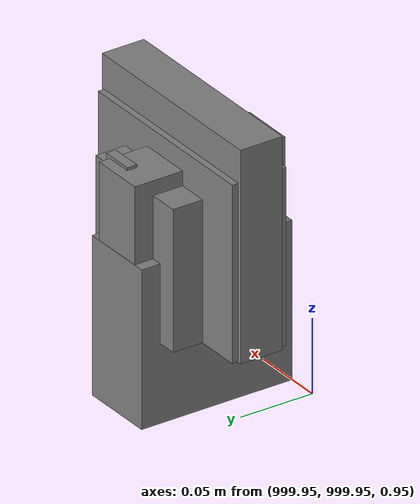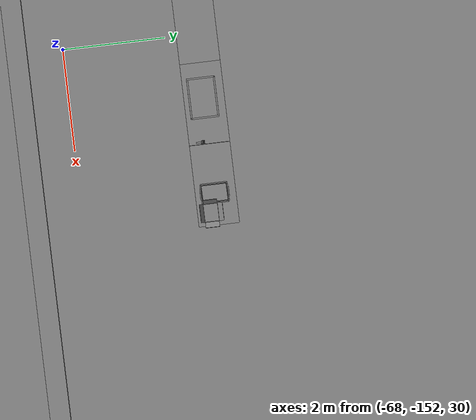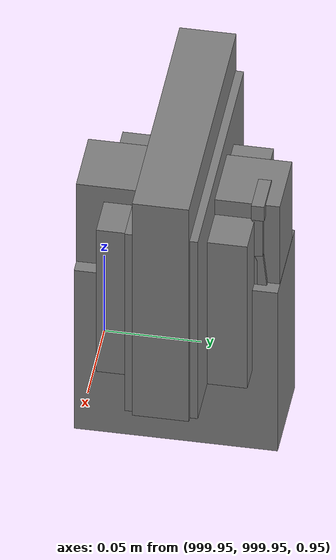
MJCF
<mujoco>
    <option gravity="0.000000000 0.000000000 -9.810000420" timestep="0.0049999999" integrator="implicitfast" density="1.225" viscosity="1.8000001e-05" noslip_iterations="10" iterations="100" sdf_iterations="50">
        <flag multiccd="disable"/>
    </option>
    <size memory="1000M"/>
    <compiler coordinate="local"/>
    <worldbody>
        <light cutoff="30" pos="0 1 1" dir="0 -1 -2"/>
        <light cutoff="30" pos="0 -1 1" dir="0 1 -2"/>
        <body pos="-64.866622925 -149.383972168 30.183746338" euler="89.999984741 89.999946594 0.000000000" name="openloong_gripper_2f85_fix_base_usda_bluebox_01">
            <geom contype="1" conaffinity="1" density="1000" type="box" material="" rgba="0.500000000 0.500000000 0.500000000 1.000000000" solimp="0.899999976 0.949999988 0.001000000" friction="1.000000000 0.005000000 0.000100000" solref="0.020000000 1.000000000" margin="0" condim="3" group="0" pos="0.276580811 0.187225342 0.000068665" quat="0.707106948 0.000077471 0.707106352 0.000077486" size="0.100000001 0.057999998 0.010000000" name="openloong_gripper_2f85_fix_base_usda_geom_E4A094B8_4543_495A_9C1F_6A28B7BD3B1F"/>
            <geom contype="1" conaffinity="1" density="1000" type="box" material="" rgba="0.500000000 0.500000000 0.500000000 1.000000000" solimp="0.899999976 0.949999988 0.001000000" friction="1.000000000 0.005000000 0.000100000" solref="0.020000000 1.000000000" margin="0" condim="3" group="0" pos="0.000000000 0.002883911 0.000000000" quat="0.999999881 0.000000000 0.000000000 0.000000000" size="0.254000008 0.003000000 0.172000006" name="openloong_gripper_2f85_fix_base_usda_geom_7FD1AEB8_50A6_467B_B62D_3CAD4245C6BD"/>
            <geom contype="1" conaffinity="1" density="1000" type="box" material="" rgba="0.500000000 0.500000000 0.500000000 1.000000000" solimp="0.899999976 0.949999988 0.001000000" friction="1.000000000 0.005000000 0.000100000" solref="0.020000000 1.000000000" margin="0" condim="3" group="0" pos="0.000000000 0.124874115 0.173484802" quat="0.999796331 0.020176515 -0.000000015 0.000000030" size="0.259999990 0.119999997 0.007000000" name="openloong_gripper_2f85_fix_base_usda_geom_23E922C5_E4A9_4AAD_AC36_077F48A395ED"/>
            <geom contype="1" conaffinity="1" density="1000" type="box" material="" rgba="0.500000000 0.500000000 0.500000000 1.000000000" solimp="0.899999976 0.949999988 0.001000000" friction="1.000000000 0.005000000 0.000100000" solref="0.020000000 1.000000000" margin="0" condim="3" group="0" pos="0.000000000 0.124874115 -0.173469543" quat="0.999796331 -0.020176545 -0.000000015 0.000000000" size="0.259999990 0.119999997 0.007000000" name="openloong_gripper_2f85_fix_base_usda_geom_B084BACA_28C7_4DBF_A64C_724ED7684A7E"/>
            <geom contype="1" conaffinity="1" density="1000" type="box" material="" rgba="0.500000000 0.500000000 0.500000000 1.000000000" solimp="0.899999976 0.949999988 0.001000000" friction="1.000000000 0.005000000 0.000100000" solref="0.020000000 1.000000000" margin="0" condim="3" group="0" pos="0.000000000 0.214008331 0.188980103" quat="0.999912977 0.013176724 0.000000015 0.000000000" size="0.259999990 0.029999999 0.012500000" name="openloong_gripper_2f85_fix_base_usda_geom_09B6F212_6AFD_4460_A3D6_1EF1298EA283"/>
            <geom contype="1" conaffinity="1" density="1000" type="box" material="" rgba="0.500000000 0.500000000 0.500000000 1.000000000" solimp="0.899999976 0.949999988 0.001000000" friction="1.000000000 0.005000000 0.000100000" solref="0.020000000 1.000000000" margin="0" condim="3" group="0" pos="-0.258361816 0.125289917 0.001876831" quat="0.702796936 -0.020792112 0.710783124 0.020769298" size="0.189999998 0.119999997 0.009000000" name="openloong_gripper_2f85_fix_base_usda_geom_D9AE88DD_DC81_42CE_95D8_F59A29B65D6F"/>
            <geom contype="1" conaffinity="1" density="1000" type="box" material="" rgba="0.500000000 0.500000000 0.500000000 1.000000000" solimp="0.899999976 0.949999988 0.001000000" friction="1.000000000 0.005000000 0.000100000" solref="0.020000000 1.000000000" margin="0" condim="3" group="0" pos="0.000000000 0.214008331 -0.188980103" quat="0.999912977 -0.013176769 0.000000030 0.000000015" size="0.259999990 0.029999999 0.012500000" name="openloong_gripper_2f85_fix_base_usda_geom_F2B25634_5760_4C15_8F36_49C365C8CC73"/>
            <geom contype="1" conaffinity="1" density="1000" type="box" material="" rgba="0.500000000 0.500000000 0.500000000 1.000000000" solimp="0.899999976 0.949999988 0.001000000" friction="1.000000000 0.005000000 0.000100000" solref="0.020000000 1.000000000" margin="0" condim="3" group="0" pos="-0.276611328 0.187225342 0.000068665" quat="0.707106650 0.000077441 0.707106709 0.000077456" size="0.100000001 0.057999998 0.010000000" name="openloong_gripper_2f85_fix_base_usda_geom_658131C0_F1A1_4705_8CC2_1F01402C8C3E"/>
            <geom contype="1" conaffinity="1" density="1000" type="box" material="" rgba="0.500000000 0.500000000 0.500000000 1.000000000" solimp="0.899999976 0.949999988 0.001000000" friction="1.000000000 0.005000000 0.000100000" solref="0.020000000 1.000000000" margin="0" condim="3" group="0" pos="0.258331299 0.125289917 0.001876831" quat="0.702851415 0.018856421 0.710823774 -0.019329369" size="0.189999998 0.119999997 0.009000000" name="openloong_gripper_2f85_fix_base_usda_geom_12C74043_7AD7_4A1D_B1AC_BAD6D54BB89F"/>
            <freejoint name="openloong_gripper_2f85_fix_base_usda_bluebox_01_joint"/>
            <site size="0.005000000 0.005000000 0.005000000" rgba="0.500000000 0.500000000 0.500000000 1.000000000" pos="0.000000000 0.000000000 0.000000000" quat="0.999961913 0.008726534 0.000000000 0.000000000" group="0" type="sphere" name="openloong_gripper_2f85_fix_base_usda_bluebox_01site"/>
        </body>
        <body pos="-64.496299744 -149.491867065 30.235729218" euler="0.000000000 0.000000000 89.999946594" name="openloong_gripper_2f85_fix_base_usda_cardboardbox_01">
            <geom contype="1" conaffinity="1" density="1000" type="box" material="" rgba="0.500000000 0.500000000 0.500000000 1.000000000" solimp="0.899999976 0.949999988 0.001000000" friction="1.000000000 0.005000000 0.000100000" solref="0.020000000 1.000000000" margin="0" condim="3" group="0" pos="-0.003166199 -0.004086494 0.005052090" quat="1.000000000 0.000000000 0.000000000 0.000000000" size="0.142499998 0.177500010 0.005000000" name="openloong_gripper_2f85_fix_base_usda_geom_786D167E_417E_4B82_9083_0F88F7CFF620"/>
            <geom contype="1" conaffinity="1" density="1000" type="box" material="" rgba="0.500000000 0.500000000 0.500000000 1.000000000" solimp="0.899999976 0.949999988 0.001000000" friction="1.000000000 0.005000000 0.000100000" solref="0.020000000 1.000000000" margin="0" condim="3" group="0" pos="-0.003166199 0.170316696 0.150570869" quat="1.000000000 0.000000000 0.000000000 0.000000000" size="0.142499998 0.005000000 0.149999991" name="openloong_gripper_2f85_fix_base_usda_geom_0D83BA18_8D65_4CEE_8F3A_047B4F7799BF"/>
            <geom contype="1" conaffinity="1" density="1000" type="box" material="" rgba="0.500000000 0.500000000 0.500000000 1.000000000" solimp="0.899999976 0.949999988 0.001000000" friction="1.000000000 0.005000000 0.000100000" solref="0.020000000 1.000000000" margin="0" condim="3" group="0" pos="-0.147399902 -0.005307198 0.150570869" quat="1.000000000 0.000000000 0.000000000 0.000000000" size="0.005000000 0.177500010 0.149999991" name="openloong_gripper_2f85_fix_base_usda_geom_00FDABFE_FD64_442C_9F22_9FE47D1F29B2"/>
            <geom contype="1" conaffinity="1" density="1000" type="box" material="" rgba="0.500000000 0.500000000 0.500000000 1.000000000" solimp="0.899999976 0.949999988 0.001000000" friction="1.000000000 0.005000000 0.000100000" solref="0.020000000 1.000000000" margin="0" condim="3" group="0" pos="0.140275955 -0.005307198 0.150570869" quat="1.000000000 0.000000000 0.000000000 0.000000000" size="0.005000000 0.177500010 0.149999991" name="openloong_gripper_2f85_fix_base_usda_geom_BBD597D3_8430_4C82_BA06_4CF95646F150"/>
            <geom contype="1" conaffinity="1" density="1000" type="box" material="" rgba="0.500000000 0.500000000 0.500000000 1.000000000" solimp="0.899999976 0.949999988 0.001000000" friction="1.000000000 0.005000000 0.000100000" solref="0.020000000 1.000000000" margin="0" condim="3" group="0" pos="-0.003166199 -0.181550980 0.150570869" quat="1.000000000 0.000000000 0.000000000 0.000000000" size="0.142499998 0.005000000 0.149999991" name="openloong_gripper_2f85_fix_base_usda_geom_877726EC_76D4_4F71_BBC4_7059366D407C"/>
            <freejoint name="openloong_gripper_2f85_fix_base_usda_cardboardbox_01_joint"/>
            <site size="0.005000000 0.005000000 0.005000000" rgba="0.500000000 0.500000000 0.500000000 1.000000000" pos="0.000000000 0.000000000 0.000000000" quat="0.999961913 0.008726535 0.000000000 0.000000000" group="0" type="sphere" name="openloong_gripper_2f85_fix_base_usda_site_A111CD85_FDB8_476F_947D_9EE9B58520D8"/>
            <body pos="0.139160156 -0.004048347 0.301930904" euler="-179.999954224 49.383502960 179.999954224" name="openloong_gripper_2f85_fix_base_usda_A1_006">
                <geom contype="1" conaffinity="1" density="1000" type="box" material="" rgba="0.500000000 0.500000000 0.500000000 1.000000000" solimp="0.899999976 0.949999988 0.001000000" friction="1.000000000 0.005000000 0.000100000" solref="0.020000000 1.000000000" margin="0" condim="3" group="0" pos="-0.071587563 0.000009537 0.001745224" quat="0.999999881 0.000000000 0.000000000 0.000000000" size="0.071249999 0.179999992 0.002500000" name="openloong_gripper_2f85_fix_base_usda_geom_3838E49C_62F5_465B_BCEA_3EB7497AB8A3"/>
                <joint armature="0" stiffness="0.07" damping="0.0099999998" axis="0.000000 1.000000 0.000000" type="hinge" name="openloong_gripper_2f85_fix_base_usda_A1_006"/>
            </body>
            <body pos="-0.145902634 -0.004086494 0.301938057" euler="-180.000000000 -60.000011444 -180.000000000" name="openloong_gripper_2f85_fix_base_usda_A2_006">
                <geom contype="1" conaffinity="1" density="1000" type="box" material="" rgba="0.500000000 0.500000000 0.500000000 1.000000000" solimp="0.899999976 0.949999988 0.001000000" friction="1.000000000 0.005000000 0.000100000" solref="0.020000000 1.000000000" margin="0" condim="3" group="0" pos="0.071268082 0.000009537 0.002717972" quat="0.000002921 0.000000000 -0.000000030 0.999999881" size="0.071249999 0.179999992 0.002500000" name="openloong_gripper_2f85_fix_base_usda_geom_66428BD0_5518_4CD0_AD5F_3A47C4622F7D"/>
                <joint armature="0" stiffness="0.07" damping="0.0099999998" axis="0.000000 1.000000 0.000000" type="hinge" name="openloong_gripper_2f85_fix_base_usda_A2_006"/>
            </body>
            <body pos="-0.003385544 0.175991058 0.301930904" euler="-125.858116150 -0.000004561 0.000002331" name="openloong_gripper_2f85_fix_base_usda_B2_006">
                <geom contype="1" conaffinity="1" density="1000" type="box" material="" rgba="0.500000000 0.500000000 0.500000000 1.000000000" solimp="0.899999976 0.949999988 0.001000000" friction="1.000000000 0.005000000 0.000100000" solref="0.020000000 1.000000000" margin="0" condim="3" group="0" pos="0.000009537 -0.070939064 -0.002470016" quat="0.999614120 0.027776197 -0.000000015 0.000000030" size="0.137500003 0.064999998 0.005000000" name="openloong_gripper_2f85_fix_base_usda_geom_45650448_E561_40D9_9186_E18AF2E8AA19"/>
                <joint armature="0" stiffness="0.07" damping="0.0099999998" axis="1.000000 0.000000 0.000000" type="hinge" name="openloong_gripper_2f85_fix_base_usda_B2_006"/>
            </body>
            <body pos="-0.003385544 -0.184140205 0.301938057" euler="147.805557251 0.000000000 0.000000000" name="openloong_gripper_2f85_fix_base_usda_B1_006">
                <geom contype="1" conaffinity="1" density="1000" type="box" material="" rgba="0.500000000 0.500000000 0.500000000 1.000000000" solimp="0.899999976 0.949999988 0.001000000" friction="1.000000000 0.005000000 0.000100000" solref="0.020000000 1.000000000" margin="0" condim="3" group="0" pos="-0.000028610 0.070202351 -0.002703667" quat="0.999614179 -0.027776167 0.000000000 0.000000000" size="0.137500003 0.064999998 0.005000000" name="openloong_gripper_2f85_fix_base_usda_geom_37E186A6_08C7_4AE0_9CFB_1F52B54F10AB"/>
                <joint armature="0" stiffness="0.07" damping="0.0099999998" axis="1.000000 0.000000 0.000000" type="hinge" name="openloong_gripper_2f85_fix_base_usda_B1_006"/>
            </body>
        </body>
        <body pos="-65.882858276 -149.481979370 30.229999542" euler="-64.487716675 0.000000000 0.000000000" name="openloong_gripper_2f85_fix_base_usda_Barcode">
            <geom contype="1" conaffinity="1" density="1000" type="box" material="" rgba="0.500000000 0.500000000 0.500000000 1.000000000" solimp="0.899999976 0.949999988 0.001000000" friction="1.000000000 0.005000000 0.000100000" solref="0.020000000 1.000000000" margin="0" condim="3" group="0" pos="0.000000000 0.013038635 0.001419067" quat="0.000000000 0.000000000 0.000000000 1.000000119" size="0.034000002 0.010000000 0.017999999" name="openloong_gripper_2f85_fix_base_usda_geom_FEBD7E32_70DC_43C4_8445_F8AE6773B0CA"/>
            <geom contype="1" conaffinity="1" density="1000" type="box" material="" rgba="0.500000000 0.500000000 0.500000000 1.000000000" solimp="0.899999976 0.949999988 0.001000000" friction="1.000000000 0.005000000 0.000100000" solref="0.020000000 1.000000000" margin="0" condim="3" group="0" pos="0.000000000 -0.035301208 -0.007095337" quat="0.000000000 0.000000000 -0.043619365 0.999048233" size="0.028999999 0.010000000 0.020000000" name="openloong_gripper_2f85_fix_base_usda_geom_B3D241F8_65F3_41F9_9EF2_083A9FE59552"/>
            <geom contype="1" conaffinity="1" density="1000" type="box" material="" rgba="0.500000000 0.500000000 0.500000000 1.000000000" solimp="0.899999976 0.949999988 0.001000000" friction="1.000000000 0.005000000 0.000100000" solref="0.020000000 1.000000000" margin="0" condim="3" group="0" pos="0.000000000 -0.043411255 -0.011749268" quat="0.922262907 0.386563420 0.000000000 0.000000000" size="0.026000001 0.010000000 0.020000000" name="openloong_gripper_2f85_fix_base_usda_geom_482F8EE3_EF4D_4AFC_B25B_A2DF6D02AE6E"/>
            <geom contype="1" conaffinity="1" density="1000" type="box" material="" rgba="0.500000000 0.500000000 0.500000000 1.000000000" solimp="0.899999976 0.949999988 0.001000000" friction="1.000000000 0.005000000 0.000100000" solref="0.020000000 1.000000000" margin="0" condim="3" group="0" pos="0.000000000 -0.016967773 -0.031860352" quat="0.000000000 0.000000000 0.000000000 1.000000119" size="0.008000000 0.010000000 0.013000000" name="openloong_gripper_2f85_fix_base_usda_geom_304B5D58_4CFB_4F39_B4F9_B74E7CE70897"/>
            <geom contype="1" conaffinity="1" density="1000" type="box" material="" rgba="0.500000000 0.500000000 0.500000000 1.000000000" solimp="0.899999976 0.949999988 0.001000000" friction="1.000000000 0.005000000 0.000100000" solref="0.020000000 1.000000000" margin="0" condim="3" group="0" pos="0.000000000 -0.001869202 0.000312805" quat="0.953716993 0.300705761 0.000000000 0.000000000" size="0.032000002 0.010000000 0.018999999" name="openloong_gripper_2f85_fix_base_usda_geom_8ADBA41C_64BA_4B40_8C73_9B02B3368883"/>
            <geom contype="1" conaffinity="1" density="1000" type="box" material="" rgba="0.500000000 0.500000000 0.500000000 1.000000000" solimp="0.899999976 0.949999988 0.001000000" friction="1.000000000 0.005000000 0.000100000" solref="0.020000000 1.000000000" margin="0" condim="3" group="0" pos="0.000000000 -0.019531250 -0.003173828" quat="0.953716993 0.300705761 0.000000000 0.000000000" size="0.030999999 0.010000000 0.020000000" name="openloong_gripper_2f85_fix_base_usda_geom_FE908A93_B7D7_4A8D_B81F_E2510AAD23AF"/>
            <geom contype="1" conaffinity="1" density="1000" type="box" material="" rgba="0.500000000 0.500000000 0.500000000 1.000000000" solimp="0.899999976 0.949999988 0.001000000" friction="1.000000000 0.005000000 0.000100000" solref="0.020000000 1.000000000" margin="0" condim="3" group="0" pos="0.000000000 -0.035301208 -0.007095337" quat="0.953716993 0.300705761 0.000000000 0.000000000" size="0.028999999 0.010000000 0.020000000" name="openloong_gripper_2f85_fix_base_usda_geom_4CC81C65_D4FB_4695_A61E_E6ED69925EDB"/>
            <geom contype="1" conaffinity="1" density="1000" type="box" material="" rgba="0.500000000 0.500000000 0.500000000 1.000000000" solimp="0.899999976 0.949999988 0.001000000" friction="1.000000000 0.005000000 0.000100000" solref="0.020000000 1.000000000" margin="0" condim="3" group="0" pos="0.000000000 -0.042617798 -0.071121216" quat="0.000000000 0.000000000 0.000000000 1.000000119" size="0.013000000 0.021000000 0.059999999" name="openloong_gripper_2f85_fix_base_usda_geom_43898E52_7C54_45E4_A3AE_A24B5BA9092E"/>
            <freejoint name="openloong_gripper_2f85_fix_base_usda_Barcode_joint"/>
            <site size="0.005000000 0.005000000 0.005000000" rgba="0.500000000 0.500000000 0.500000000 1.000000000" pos="0.000000000 0.000000000 0.000000000" quat="1.000000000 0.000000000 0.000000000 0.000000000" group="0" type="sphere" name="openloong_gripper_2f85_fix_base_usda_Barcode_site"/>
        </body>
        <body pos="-66.745018005 -149.392349243 30.184000015" euler="0.000000000 0.000000000 89.999946594" name="[22330357687291]_Basket_01">
            <geom contype="1" conaffinity="1" density="1000" type="box" material="" rgba="0.500000000 0.500000000 0.500000000 1.000000000" solimp="0.899999976 0.949999988 0.001000000" friction="1.000000000 0.005000000 0.000100000" solref="0.020000000 1.000000000" margin="0" condim="3" group="0" pos="-0.052425385 0.389207840 0.089787483" quat="0.707107008 0.000000000 0.000000000 0.707106411" size="0.014249999 0.014249999 0.059999999" name="[22330357687291]_geom_F3645EE6_2339_4C0E_9BAB_21A6711C4B8E"/>
            <geom contype="1" conaffinity="1" density="1000" type="box" material="" rgba="0.500000000 0.500000000 0.500000000 1.000000000" solimp="0.899999976 0.949999988 0.001000000" friction="1.000000000 0.005000000 0.000100000" solref="0.020000000 1.000000000" margin="0" condim="3" group="0" pos="0.264015198 -0.133043289 0.089787483" quat="0.707107008 0.000000000 0.000000000 0.707106411" size="0.014249999 0.014249999 0.059999999" name="[22330357687291]_geom_D301E364_CA32_4257_AAC0_2A6FD3AC26E0"/>
            <geom contype="1" conaffinity="1" density="1000" type="box" material="" rgba="0.500000000 0.500000000 0.500000000 1.000000000" solimp="0.899999976 0.949999988 0.001000000" friction="1.000000000 0.005000000 0.000100000" solref="0.020000000 1.000000000" margin="0" condim="3" group="0" pos="-0.264015198 -0.265548706 0.089793205" quat="0.707107008 0.000000000 0.000000000 0.707106411" size="0.014249999 0.014249999 0.059999999" name="[22330357687291]_geom_F09D1D9B_F6B0_4C2D_B1D6_49743325B5F2"/>
            <geom contype="1" conaffinity="1" density="1000" type="box" material="" rgba="0.500000000 0.500000000 0.500000000 1.000000000" solimp="0.899999976 0.949999988 0.001000000" friction="1.000000000 0.005000000 0.000100000" solref="0.020000000 1.000000000" margin="0" condim="3" group="0" pos="-0.160263062 -0.389322281 0.089793205" quat="0.707107008 0.000000000 0.000000000 0.707106411" size="0.014249999 0.014249999 0.059999999" name="[22330357687291]_geom_28E55806_10DC_42A2_A77F_135D2C3B35E4"/>
            <geom contype="1" conaffinity="1" density="1000" type="box" material="" rgba="0.500000000 0.500000000 0.500000000 1.000000000" solimp="0.899999976 0.949999988 0.001000000" friction="1.000000000 0.005000000 0.000100000" solref="0.020000000 1.000000000" margin="0" condim="3" group="0" pos="0.162265778 -0.389322281 0.089787483" quat="0.707107008 0.000000000 0.000000000 0.707106411" size="0.014249999 0.014249999 0.059999999" name="[22330357687291]_geom_6F0C542E_E6FA_48C5_A1CC_465948583BFF"/>
            <geom contype="1" conaffinity="1" density="1000" type="box" material="" rgba="0.500000000 0.500000000 0.500000000 1.000000000" solimp="0.899999976 0.949999988 0.001000000" friction="1.000000000 0.005000000 0.000100000" solref="0.020000000 1.000000000" margin="0" condim="3" group="0" pos="0.264015198 0.389207840 0.089787483" quat="0.707107008 0.000000000 0.000000000 0.707106411" size="0.014249999 0.014249999 0.059999999" name="[22330357687291]_geom_5FBCA56C_A5F2_4DDE_BE98_E5F3870A42E1"/>
            <geom contype="1" conaffinity="1" density="1000" type="box" material="" rgba="0.500000000 0.500000000 0.500000000 1.000000000" solimp="0.899999976 0.949999988 0.001000000" friction="1.000000000 0.005000000 0.000100000" solref="0.020000000 1.000000000" margin="0" condim="3" group="0" pos="-0.264015198 -0.133043289 0.089793205" quat="0.707107008 0.000000000 0.000000000 0.707106411" size="0.014249999 0.014249999 0.059999999" name="[22330357687291]_geom_A74E69D8_2493_484C_B478_A6939DAA2399"/>
            <geom contype="1" conaffinity="1" density="1000" type="box" material="" rgba="0.500000000 0.500000000 0.500000000 1.000000000" solimp="0.899999976 0.949999988 0.001000000" friction="1.000000000 0.005000000 0.000100000" solref="0.020000000 1.000000000" margin="0" condim="3" group="0" pos="-0.264026642 0.269256592 0.089793205" quat="0.707107008 0.000000000 0.000000000 0.707106411" size="0.014249999 0.014249999 0.059999999" name="[22330357687291]_geom_664C66F2_930C_4972_B424_D75D5D9D7792"/>
            <geom contype="1" conaffinity="1" density="1000" type="box" material="" rgba="0.500000000 0.500000000 0.500000000 1.000000000" solimp="0.899999976 0.949999988 0.001000000" friction="1.000000000 0.005000000 0.000100000" solref="0.020000000 1.000000000" margin="0" condim="3" group="0" pos="0.054462433 0.389207840 0.089787483" quat="0.707107008 0.000000000 0.000000000 0.707106411" size="0.014249999 0.014249999 0.059999999" name="[22330357687291]_geom_E8C26706_2EDE_48D0_9E42_CBD74EF90F18"/>
            <geom contype="1" conaffinity="1" density="1000" type="box" material="" rgba="0.500000000 0.500000000 0.500000000 1.000000000" solimp="0.899999976 0.949999988 0.001000000" friction="1.000000000 0.005000000 0.000100000" solref="0.020000000 1.000000000" margin="0" condim="3" group="0" pos="0.054462433 -0.389322281 0.089787483" quat="0.707107008 0.000000000 0.000000000 0.707106411" size="0.014249999 0.014249999 0.059999999" name="[22330357687291]_geom_ED7DD59B_56A2_4A55_9EDF_65E2E37C8D6D"/>
            <geom contype="1" conaffinity="1" density="1000" type="box" material="" rgba="0.500000000 0.500000000 0.500000000 1.000000000" solimp="0.899999976 0.949999988 0.001000000" friction="1.000000000 0.005000000 0.000100000" solref="0.020000000 1.000000000" margin="0" condim="3" group="0" pos="0.264015198 0.269256592 0.089793205" quat="0.707107008 0.000000000 0.000000000 0.707106411" size="0.014249999 0.014249999 0.059999999" name="[22330357687291]_geom_8F506654_1217_4DD7_AFCD_DA9F995D74FD"/>
            <geom contype="1" conaffinity="1" density="1000" type="box" material="" rgba="0.500000000 0.500000000 0.500000000 1.000000000" solimp="0.899999976 0.949999988 0.001000000" friction="1.000000000 0.005000000 0.000100000" solref="0.020000000 1.000000000" margin="0" condim="3" group="0" pos="0.264015198 -0.389322281 0.089787483" quat="0.707107008 0.000000000 0.000000000 0.707106411" size="0.014249999 0.014249999 0.059999999" name="[22330357687291]_geom_4A40CDFB_5DED_48A7_B980_31495934D4DB"/>
            <geom contype="1" conaffinity="1" density="1000" type="box" material="" rgba="0.500000000 0.500000000 0.500000000 1.000000000" solimp="0.899999976 0.949999988 0.001000000" friction="1.000000000 0.005000000 0.000100000" solref="0.020000000 1.000000000" margin="0" condim="3" group="0" pos="0.000000000 0.000000000 0.015998840" quat="0.707107008 0.000000000 0.000000000 0.707106411" size="0.403499991 0.279000014 0.015750000" name="[22330357687291]_geom_5BFC875B_5764_48A9_B24E_84DECC3C17CE"/>
            <geom contype="1" conaffinity="1" density="1000" type="box" material="" rgba="0.500000000 0.500000000 0.500000000 1.000000000" solimp="0.899999976 0.949999988 0.001000000" friction="1.000000000 0.005000000 0.000100000" solref="0.020000000 1.000000000" margin="0" condim="3" group="0" pos="0.000000000 -0.389476776 0.163619041" quat="0.707107008 0.000000000 0.000000000 0.707106411" size="0.015000000 0.277500004 0.015750000" name="[22330357687291]_geom_3F05B648_532A_468E_BD20_AC7A507DB90E"/>
            <geom contype="1" conaffinity="1" density="1000" type="box" material="" rgba="0.500000000 0.500000000 0.500000000 1.000000000" solimp="0.899999976 0.949999988 0.001000000" friction="1.000000000 0.005000000 0.000100000" solref="0.020000000 1.000000000" margin="0" condim="3" group="0" pos="0.162265778 0.389207840 0.089787483" quat="0.707107008 0.000000000 0.000000000 0.707106411" size="0.014249999 0.014249999 0.059999999" name="[22330357687291]_geom_B6A47742_BB41_43BF_A7FC_2F072C3C341E"/>
            <geom contype="1" conaffinity="1" density="1000" type="box" material="" rgba="0.500000000 0.500000000 0.500000000 1.000000000" solimp="0.899999976 0.949999988 0.001000000" friction="1.000000000 0.005000000 0.000100000" solref="0.020000000 1.000000000" margin="0" condim="3" group="0" pos="0.000000000 0.389471054 0.163619041" quat="0.707107008 0.000000000 0.000000000 0.707106411" size="0.015000000 0.277500004 0.015750000" name="[22330357687291]_geom_25D7C8F8_4EF2_4D3F_A4C0_5D4463805C8A"/>
            <geom contype="1" conaffinity="1" density="1000" type="box" material="" rgba="0.500000000 0.500000000 0.500000000 1.000000000" solimp="0.899999976 0.949999988 0.001000000" friction="1.000000000 0.005000000 0.000100000" solref="0.020000000 1.000000000" margin="0" condim="3" group="0" pos="-0.263511658 0.000000000 0.163619041" quat="0.707107008 0.000000000 0.000000000 0.707106411" size="0.403499991 0.015000000 0.015750000" name="[22330357687291]_geom_5C24E81A_7D33_43A3_B4A9_D78C4F7030D4"/>
            <geom contype="1" conaffinity="1" density="1000" type="box" material="" rgba="0.500000000 0.500000000 0.500000000 1.000000000" solimp="0.899999976 0.949999988 0.001000000" friction="1.000000000 0.005000000 0.000100000" solref="0.020000000 1.000000000" margin="0" condim="3" group="0" pos="-0.264015198 0.141334534 0.089793205" quat="0.707107008 0.000000000 0.000000000 0.707106411" size="0.014249999 0.014249999 0.059999999" name="[22330357687291]_geom_04BB6751_542E_40F2_8B82_8789A007DADE"/>
            <geom contype="1" conaffinity="1" density="1000" type="box" material="" rgba="0.500000000 0.500000000 0.500000000 1.000000000" solimp="0.899999976 0.949999988 0.001000000" friction="1.000000000 0.005000000 0.000100000" solref="0.020000000 1.000000000" margin="0" condim="3" group="0" pos="0.264015198 -0.265548706 0.089787483" quat="0.707107008 0.000000000 0.000000000 0.707106411" size="0.014249999 0.014249999 0.059999999" name="[22330357687291]_geom_BF09DD32_F0D7_4D91_8DBC_0C462CD574A0"/>
            <geom contype="1" conaffinity="1" density="1000" type="box" material="" rgba="0.500000000 0.500000000 0.500000000 1.000000000" solimp="0.899999976 0.949999988 0.001000000" friction="1.000000000 0.005000000 0.000100000" solref="0.020000000 1.000000000" margin="0" condim="3" group="0" pos="-0.160263062 0.389207840 0.089787483" quat="0.707107008 0.000000000 0.000000000 0.707106411" size="0.014249999 0.014249999 0.059999999" name="[22330357687291]_geom_4892D409_E7C0_4146_8C50_D3F8A6A21B56"/>
            <geom contype="1" conaffinity="1" density="1000" type="box" material="" rgba="0.500000000 0.500000000 0.500000000 1.000000000" solimp="0.899999976 0.949999988 0.001000000" friction="1.000000000 0.005000000 0.000100000" solref="0.020000000 1.000000000" margin="0" condim="3" group="0" pos="-0.052425385 -0.389322281 0.089787483" quat="0.707107008 0.000000000 0.000000000 0.707106411" size="0.014249999 0.014249999 0.059999999" name="[22330357687291]_geom_0660D68D_63B8_4E60_A1C5_AC0056FE7C0B"/>
            <geom contype="1" conaffinity="1" density="1000" type="box" material="" rgba="0.500000000 0.500000000 0.500000000 1.000000000" solimp="0.899999976 0.949999988 0.001000000" friction="1.000000000 0.005000000 0.000100000" solref="0.020000000 1.000000000" margin="0" condim="3" group="0" pos="-0.264026642 -0.389322281 0.089793205" quat="0.707107008 0.000000000 0.000000000 0.707106411" size="0.014249999 0.014249999 0.059999999" name="[22330357687291]_geom_3F9F69FD_8BD1_412D_BA09_1BF2E3E10E16"/>
            <geom contype="1" conaffinity="1" density="1000" type="box" material="" rgba="0.500000000 0.500000000 0.500000000 1.000000000" solimp="0.899999976 0.949999988 0.001000000" friction="1.000000000 0.005000000 0.000100000" solref="0.020000000 1.000000000" margin="0" condim="3" group="0" pos="0.264015198 0.141334534 0.089787483" quat="0.707107008 0.000000000 0.000000000 0.707106411" size="0.014249999 0.014249999 0.059999999" name="[22330357687291]_geom_93B88185_3884_4462_AEB5_D5A26A29549D"/>
            <geom contype="1" conaffinity="1" density="1000" type="box" material="" rgba="0.500000000 0.500000000 0.500000000 1.000000000" solimp="0.899999976 0.949999988 0.001000000" friction="1.000000000 0.005000000 0.000100000" solref="0.020000000 1.000000000" margin="0" condim="3" group="0" pos="-0.264015198 0.389207840 0.089793205" quat="0.707107008 0.000000000 0.000000000 0.707106411" size="0.014249999 0.014249999 0.059999999" name="[22330357687291]_geom_9A86CFE9_3CC5_426B_98FF_06135B2978CB"/>
            <geom contype="1" conaffinity="1" density="1000" type="box" material="" rgba="0.500000000 0.500000000 0.500000000 1.000000000" solimp="0.899999976 0.949999988 0.001000000" friction="1.000000000 0.005000000 0.000100000" solref="0.020000000 1.000000000" margin="0" condim="3" group="0" pos="0.264015198 0.004480362 0.089787483" quat="0.707107008 0.000000000 0.000000000 0.707106411" size="0.014249999 0.014249999 0.059999999" name="[22330357687291]_geom_904E7B17_3E12_4C17_AC70_B5F3D9E6718C"/>
            <geom contype="1" conaffinity="1" density="1000" type="box" material="" rgba="0.500000000 0.500000000 0.500000000 1.000000000" solimp="0.899999976 0.949999988 0.001000000" friction="1.000000000 0.005000000 0.000100000" solref="0.020000000 1.000000000" margin="0" condim="3" group="0" pos="0.263694763 -0.000011444 0.163619041" quat="0.707107008 0.000000000 0.000000000 0.707106411" size="0.403499991 0.015000000 0.015750000" name="[22330357687291]_geom_A8402FA3_D88B_44DE_BCBB_01A2A6236A3A"/>
            <geom contype="1" conaffinity="1" density="1000" type="box" material="" rgba="0.500000000 0.500000000 0.500000000 1.000000000" solimp="0.899999976 0.949999988 0.001000000" friction="1.000000000 0.005000000 0.000100000" solref="0.020000000 1.000000000" margin="0" condim="3" group="0" pos="-0.264015198 0.004480362 0.089793205" quat="0.707107008 0.000000000 0.000000000 0.707106411" size="0.014249999 0.014249999 0.059999999" name="[22330357687291]_geom_73975BE0_E25A_4E1C_A6DE_545ACF2698B3"/>
            <freejoint name="[22330357687291]_joint_3E11C54D_13BB_47EB_BEB5_ED635084F9A0"/>
        </body>
        <body pos="0.000000000 0.000000000 0.000000000" euler="0.000000000 0.000000000 0.000000000" name="Static Objects_Static Objects">
            <geom contype="1" conaffinity="1" density="1000" type="box" material="" rgba="0.500000000 0.500000000 0.500000000 1.000000000" solimp="0.899999976 0.949999988 0.001000000" friction="1.000000000 0.005000000 0.000100000" solref="0.020000000 1.000000000" margin="0" condim="3" group="0" pos="-67.544113159 -149.365814209 29.727830887" quat="0.500000417 0.499999970 0.499999553 0.499999970" size="0.381000012 0.319999993 0.041000001" name="Static Objects_geom_605B44B6_B46C_4991_B996_BB99EDB01A17"/>
            <geom contype="1" conaffinity="1" density="1000" type="box" material="" rgba="0.500000000 0.500000000 0.500000000 1.000000000" solimp="0.899999976 0.949999988 0.001000000" friction="1.000000000 0.005000000 0.000100000" solref="0.020000000 1.000000000" margin="0" condim="3" group="0" pos="-68.239501953 -149.365814209 30.086868286" quat="0.500000417 0.499999970 0.499999553 0.499999970" size="0.370999992 0.039500002 0.745000005" name="Static Objects_geom_F99CF2D9_05DB_434F_AF36_E7CC18812640"/>
            <geom contype="1" conaffinity="1" density="1000" type="box" material="" rgba="0.500000000 0.500000000 0.500000000 1.000000000" solimp="0.899999976 0.949999988 0.001000000" friction="1.000000000 0.005000000 0.000100000" solref="0.020000000 1.000000000" margin="0" condim="3" group="0" pos="-68.239501953 -149.365814209 30.147235870" quat="0.500000417 0.499999970 0.499999553 0.499999970" size="0.400000006 0.022000000 0.800000012" name="Static Objects_geom_66EDECF4_844D_467F_8807_38B57E3B428D"/>
            <geom contype="1" conaffinity="1" density="1000" type="box" material="" rgba="0.500000000 0.500000000 0.500000000 1.000000000" solimp="0.899999976 0.949999988 0.001000000" friction="1.000000000 0.005000000 0.000100000" solref="0.020000000 1.000000000" margin="0" condim="3" group="0" pos="-68.934890747 -149.365814209 29.727830887" quat="0.500000417 0.499999970 0.499999553 0.499999970" size="0.381000012 0.319999993 0.041000001" name="Static Objects_geom_AAA2DC6A_5995_486C_852C_2B5B96E67F07"/>
            <geom contype="1" conaffinity="1" density="1000" type="box" material="" rgba="0.500000000 0.500000000 0.500000000 1.000000000" solimp="0.899999976 0.949999988 0.001000000" friction="1.000000000 0.005000000 0.000100000" solref="0.020000000 1.000000000" margin="0" condim="3" group="0" pos="-68.239501953 -149.365814209 29.561563492" quat="0.500000417 0.499999970 0.499999553 0.499999970" size="0.020000000 0.022000000 0.660000026" name="Static Objects_geom_44B5AACE_A36D_4224_8889_AA6EB56FD4F7"/>
            <geom contype="1" conaffinity="1" density="1000" type="box" material="" rgba="0.500000000 0.500000000 0.500000000 1.000000000" solimp="0.899999976 0.949999988 0.001000000" friction="1.000000000 0.005000000 0.000100000" solref="0.020000000 1.000000000" margin="0" condim="3" group="0" pos="-65.945671082 -149.365814209 29.727830887" quat="0.500000417 0.499999970 0.499999553 0.499999970" size="0.381000012 0.319999993 0.041000001" name="Static Objects_geom_A18F0839_9C30_4880_ADC2_10BE460AF900"/>
            <geom contype="1" conaffinity="1" density="1000" type="box" material="" rgba="0.500000000 0.500000000 0.500000000 1.000000000" solimp="0.899999976 0.949999988 0.001000000" friction="1.000000000 0.005000000 0.000100000" solref="0.020000000 1.000000000" margin="0" condim="3" group="0" pos="-66.641059875 -149.365814209 30.086868286" quat="0.500000417 0.499999970 0.499999553 0.499999970" size="0.370999992 0.039500002 0.745000005" name="Static Objects_geom_B80F1BCB_84F9_45DA_A4DF_303518340147"/>
            <geom contype="1" conaffinity="1" density="1000" type="box" material="" rgba="0.500000000 0.500000000 0.500000000 1.000000000" solimp="0.899999976 0.949999988 0.001000000" friction="1.000000000 0.005000000 0.000100000" solref="0.020000000 1.000000000" margin="0" condim="3" group="0" pos="-66.641059875 -149.365814209 30.147235870" quat="0.500000417 0.499999970 0.499999553 0.499999970" size="0.400000006 0.022000000 0.800000012" name="Static Objects_geom_EE3A8133_2600_41AD_B402_A6436B4E70F5"/>
            <geom contype="1" conaffinity="1" density="1000" type="box" material="" rgba="0.500000000 0.500000000 0.500000000 1.000000000" solimp="0.899999976 0.949999988 0.001000000" friction="1.000000000 0.005000000 0.000100000" solref="0.020000000 1.000000000" margin="0" condim="3" group="0" pos="-67.336448669 -149.365814209 29.727830887" quat="0.500000417 0.499999970 0.499999553 0.499999970" size="0.381000012 0.319999993 0.041000001" name="Static Objects_geom_41ABF6D2_3EBF_4DA6_AF24_D9EBA5333AED"/>
            <geom contype="1" conaffinity="1" density="1000" type="box" material="" rgba="0.500000000 0.500000000 0.500000000 1.000000000" solimp="0.899999976 0.949999988 0.001000000" friction="1.000000000 0.005000000 0.000100000" solref="0.020000000 1.000000000" margin="0" condim="3" group="0" pos="-66.641059875 -149.365814209 29.561563492" quat="0.500000417 0.499999970 0.499999553 0.499999970" size="0.020000000 0.022000000 0.660000026" name="Static Objects_geom_0D5DC3EA_55E7_4360_9F9B_9D432FE6E2C1"/>
            <geom contype="1" conaffinity="1" density="1000" type="box" material="" rgba="0.500000000 0.500000000 0.500000000 1.000000000" solimp="0.899999976 0.949999988 0.001000000" friction="1.000000000 0.005000000 0.000100000" solref="0.020000000 1.000000000" margin="0" condim="3" group="0" pos="-64.338577271 -149.365814209 29.727830887" quat="0.500000417 0.499999970 0.499999553 0.499999970" size="0.381000012 0.319999993 0.041000001" name="Static Objects_geom_112256DF_38C8_4483_844B_24DA3AF3DE34"/>
            <geom contype="1" conaffinity="1" density="1000" type="box" material="" rgba="0.500000000 0.500000000 0.500000000 1.000000000" solimp="0.899999976 0.949999988 0.001000000" friction="1.000000000 0.005000000 0.000100000" solref="0.020000000 1.000000000" margin="0" condim="3" group="0" pos="-65.033966064 -149.365814209 30.086868286" quat="0.500000417 0.499999970 0.499999553 0.499999970" size="0.370999992 0.039500002 0.745000005" name="Static Objects_geom_0E18026F_642C_4B7D_9878_7996764FD38C"/>
            <geom contype="1" conaffinity="1" density="1000" type="box" material="" rgba="0.500000000 0.500000000 0.500000000 1.000000000" solimp="0.899999976 0.949999988 0.001000000" friction="1.000000000 0.005000000 0.000100000" solref="0.020000000 1.000000000" margin="0" condim="3" group="0" pos="-65.033966064 -149.365814209 30.147235870" quat="0.500000417 0.499999970 0.499999553 0.499999970" size="0.400000006 0.022000000 0.800000012" name="Static Objects_geom_D37C0EA5_F718_4F49_9FA6_1A3111C1E85F"/>
            <geom contype="1" conaffinity="1" density="1000" type="box" material="" rgba="0.500000000 0.500000000 0.500000000 1.000000000" solimp="0.899999976 0.949999988 0.001000000" friction="1.000000000 0.005000000 0.000100000" solref="0.020000000 1.000000000" margin="0" condim="3" group="0" pos="-65.729354858 -149.365814209 29.727830887" quat="0.500000417 0.499999970 0.499999553 0.499999970" size="0.381000012 0.319999993 0.041000001" name="Static Objects_geom_F86C4D6C_3A5A_4482_B336_F0E9F0811103"/>
            <geom contype="1" conaffinity="1" density="1000" type="box" material="" rgba="0.500000000 0.500000000 0.500000000 1.000000000" solimp="0.899999976 0.949999988 0.001000000" friction="1.000000000 0.005000000 0.000100000" solref="0.020000000 1.000000000" margin="0" condim="3" group="0" pos="-65.033966064 -149.365814209 29.561563492" quat="0.500000417 0.499999970 0.499999553 0.499999970" size="0.020000000 0.022000000 0.660000026" name="Static Objects_geom_1F08DBF4_CF73_4E1E_B171_CB7FCD9E2002"/>
            <geom contype="1" conaffinity="1" density="1000" type="box" material="" rgba="0.500000000 0.500000000 0.500000000 1.000000000" solimp="0.899999976 0.949999988 0.001000000" friction="1.000000000 0.005000000 0.000100000" solref="0.020000000 1.000000000" margin="0" condim="3" group="0" pos="-61.754566193 -137.853729248 33.906845093" quat="0.707107067 0.000000000 0.000000000 0.707106471" size="0.759999990 0.759999990 4.500000000" name="Static Objects_geom_A6A4CB96_19E8_48D8_8A3E_43534F9DE27F"/>
            <geom contype="1" conaffinity="1" density="1000" type="box" material="" rgba="0.500000000 0.500000000 0.500000000 1.000000000" solimp="0.899999976 0.949999988 0.001000000" friction="1.000000000 0.005000000 0.000100000" solref="0.020000000 1.000000000" margin="0" condim="3" group="0" pos="-57.511135101 -144.927108765 31.707921982" quat="1.000000000 0.000000000 0.000000000 0.000000000" size="0.200000003 8.000000000 2.299999952" name="Static Objects_geom_D267BB1F_8F42_4C6C_A6AB_5CF7C9FDB2AC"/>
            <geom contype="1" conaffinity="1" density="1000" type="box" material="" rgba="0.500000000 0.500000000 0.500000000 1.000000000" solimp="0.899999976 0.949999988 0.001000000" friction="1.000000000 0.005000000 0.000100000" solref="0.020000000 1.000000000" margin="0" condim="3" group="0" pos="-80.517646790 -157.574050903 31.688196182" quat="0.707107067 0.000000000 0.000000000 0.707106471" size="0.600000024 0.600000024 2.299999952" name="Static Objects_geom_1256838C_F188_4382_8B7B_9780F12F4D01"/>
            <geom contype="1" conaffinity="1" density="1000" type="box" material="" rgba="0.500000000 0.500000000 0.500000000 1.000000000" solimp="0.899999976 0.949999988 0.001000000" friction="1.000000000 0.005000000 0.000100000" solref="0.020000000 1.000000000" margin="0" condim="3" group="0" pos="-80.711044312 -147.414932251 31.666158676" quat="1.000000000 0.000000000 0.000000000 0.000000000" size="0.200000003 10.000000000 2.299999952" name="Static Objects_geom_E6E93AB0_21D9_44C6_A5FF_131C5D76D6CA"/>
            <geom contype="1" conaffinity="1" density="1000" type="box" material="" rgba="0.500000000 0.500000000 0.500000000 1.000000000" solimp="0.899999976 0.949999988 0.001000000" friction="1.000000000 0.005000000 0.000100000" solref="0.020000000 1.000000000" margin="0" condim="3" group="0" pos="-57.687217712 -137.434692383 31.688196182" quat="0.707107067 0.000000000 0.000000000 0.707106471" size="0.600000024 0.600000024 2.299999952" name="Static Objects_geom_6E293186_0085_42F6_B268_E75606F2CCA0"/>
            <geom contype="1" conaffinity="1" density="1000" type="box" material="" rgba="0.500000000 0.500000000 0.500000000 1.000000000" solimp="0.899999976 0.949999988 0.001000000" friction="1.000000000 0.005000000 0.000100000" solref="0.020000000 1.000000000" margin="0" condim="3" group="0" pos="-69.537033081 -140.263229370 31.714921951" quat="0.707107067 0.000000000 0.000000000 0.707106471" size="0.759999990 4.500000000 2.299999952" name="Static Objects_geom_500D2200_9C4E_4993_8175_53AEC6F64245"/>
            <geom contype="1" conaffinity="1" density="1000" type="box" material="" rgba="0.500000000 0.500000000 0.500000000 1.000000000" solimp="0.899999976 0.949999988 0.001000000" friction="1.000000000 0.005000000 0.000100000" solref="0.020000000 1.000000000" margin="0" condim="3" group="0" pos="-80.073638916 -137.853713989 33.906845093" quat="0.707107067 0.000000000 0.000000000 0.707106471" size="0.759999990 0.759999990 4.500000000" name="Static Objects_geom_6AAA05E2_D033_467A_8DB9_CD735FB5B287"/>
            <geom contype="1" conaffinity="1" density="1000" type="box" material="" rgba="0.500000000 0.500000000 0.500000000 1.000000000" solimp="0.899999976 0.949999988 0.001000000" friction="1.000000000 0.005000000 0.000100000" solref="0.020000000 1.000000000" margin="0" condim="3" group="0" pos="-73.406707764 -155.734664917 31.707921982" quat="1.000000000 0.000000000 0.000000000 0.000000000" size="0.200000003 3.000000000 2.299999952" name="Static Objects_geom_435408EC_BA0A_4D2C_AFE2_BBD435A2138C"/>
            <geom contype="1" conaffinity="1" density="1000" type="box" material="" rgba="0.500000000 0.500000000 0.500000000 1.000000000" solimp="0.899999976 0.949999988 0.001000000" friction="1.000000000 0.005000000 0.000100000" solref="0.020000000 1.000000000" margin="0" condim="3" group="0" pos="-68.497543335 -137.448257446 31.707921982" quat="0.707107067 0.000000000 0.000000000 0.707106471" size="0.200000003 14.000000000 2.299999952" name="Static Objects_geom_B60BA803_03FB_4FDF_B040_96E2658EE2C2"/>
            <geom contype="1" conaffinity="1" density="1000" type="cylinder" material="" rgba="0.500000000 0.500000000 0.500000000 1.000000000" solimp="0.899999976 0.949999988 0.001000000" friction="1.000000000 0.005000000 0.000100000" solref="0.020000000 1.000000000" margin="0" condim="3" group="0" pos="-68.868522644 -142.134506226 31.711090088" quat="0.707107067 0.000000000 0.000000000 0.707106471" size="0.509999990 2.299999952 1.000000000" name="Static Objects_geom_1DF0E7C3_81A7_4CCC_94FC_CE8AF5BAD348"/>
            <geom contype="1" conaffinity="1" density="1000" type="plane" material="" rgba="0.500000000 0.500000000 0.500000000 1.000000000" solimp="0.899999976 0.949999988 0.001000000" friction="1.000000000 0.005000000 0.000100000" solref="0.020000000 1.000000000" margin="0" condim="3" group="0" pos="-72.873703003 -147.131927490 29.409669876" quat="1.000000000 0.000000000 0.000000000 0.000000000" size="18.000000000 14.000000000 1.000000000" name="Static Objects_geom_DCDA1022_582D_4757_84DC_6FB7DCBB4D63"/>
            <geom contype="1" conaffinity="1" density="1000" type="box" material="" rgba="0.500000000 0.500000000 0.500000000 1.000000000" solimp="0.899999976 0.949999988 0.001000000" friction="1.000000000 0.005000000 0.000100000" solref="0.020000000 1.000000000" margin="0" condim="3" group="0" pos="-79.943580627 -157.782272339 31.707921982" quat="0.707107067 0.000000000 0.000000000 0.707106471" size="0.200000003 7.000000000 2.299999952" name="Static Objects_geom_2B8DCA00_14AA_430E_B48C_DF00BEC17387"/>
            <geom contype="1" conaffinity="1" density="1000" type="box" material="" rgba="0.500000000 0.500000000 0.500000000 1.000000000" solimp="0.899999976 0.949999988 0.001000000" friction="1.000000000 0.005000000 0.000100000" solref="0.020000000 1.000000000" margin="0" condim="3" group="0" pos="-65.421028137 -152.903442383 31.707921982" quat="0.707107067 0.000000000 0.000000000 0.707106471" size="0.200000003 7.800000191 2.299999952" name="Static Objects_geom_4A06A9F1_6317_45C5_ADC2_7DF284BE00EB"/>
            <geom contype="1" conaffinity="1" density="1000" type="box" material="" rgba="0.500000000 0.500000000 0.500000000 1.000000000" solimp="0.899999976 0.949999988 0.001000000" friction="1.000000000 0.005000000 0.000100000" solref="0.020000000 1.000000000" margin="0" condim="3" group="0" pos="-74.776908875 -149.964416504 31.688196182" quat="1.000000000 0.000000000 0.000000000 0.000000000" size="0.600000024 0.409999996 2.299999952" name="Static Objects_geom_FBBBA00B_013D_4332_B2A9_1D7057CD463F"/>
            <geom contype="1" conaffinity="1" density="1000" type="cylinder" material="" rgba="0.500000000 0.500000000 0.500000000 1.000000000" solimp="0.899999976 0.949999988 0.001000000" friction="1.000000000 0.005000000 0.000100000" solref="0.020000000 1.000000000" margin="0" condim="3" group="0" pos="-60.161884308 -142.134506226 31.711090088" quat="0.707107067 0.000000000 0.000000000 0.707106471" size="0.509999990 2.299999952 1.000000000" name="Static Objects_geom_CA9ADF1E_323E_4FC5_8D31_F7F2DAF0B3EC"/>
            <geom contype="1" conaffinity="1" density="1000" type="cylinder" material="" rgba="0.500000000 0.500000000 0.500000000 1.000000000" solimp="0.899999976 0.949999988 0.001000000" friction="1.000000000 0.005000000 0.000100000" solref="0.020000000 1.000000000" margin="0" condim="3" group="0" pos="-75.382453918 -149.963455200 31.711090088" quat="0.707107067 0.000000000 0.000000000 0.707106471" size="0.409999996 2.299999952 1.000000000" name="Static Objects_geom_3C5B4E01_32F7_4F0A_8975_180E8FC0B9F4"/>
            <geom contype="1" conaffinity="1" density="1000" type="cylinder" material="" rgba="0.500000000 0.500000000 0.500000000 1.000000000" solimp="0.899999976 0.949999988 0.001000000" friction="1.000000000 0.005000000 0.000100000" solref="0.020000000 1.000000000" margin="0" condim="3" group="0" pos="-74.154960632 -149.963455200 31.711090088" quat="0.707107067 0.000000000 0.000000000 0.707106471" size="0.409999996 2.299999952 1.000000000" name="Static Objects_geom_F97DD323_21FC_46F0_9956_39596743B2EA"/>
            <geom contype="1" conaffinity="1" density="1000" type="cylinder" material="" rgba="0.500000000 0.500000000 0.500000000 1.000000000" solimp="0.899999976 0.949999988 0.001000000" friction="1.000000000 0.005000000 0.000100000" solref="0.020000000 1.000000000" margin="0" condim="3" group="0" pos="-77.566612244 -142.134506226 31.711090088" quat="0.707107067 0.000000000 0.000000000 0.707106471" size="0.509999990 2.299999952 1.000000000" name="Static Objects_geom_31BD79BC_FB93_4C40_99CE_9A796C856771"/>
        </body>
        <body pos="1000.000000000 1000.000000000 1.000000000" euler="0.000000000 0.000000000 180.000000000" name="openloong_gripper_2f85_fix_base_usda_wifi_box">
            <geom contype="1" conaffinity="1" density="1000" type="box" material="" rgba="0.500000000 0.500000000 0.500000000 1.000000000" solimp="0.899999976 0.949999988 0.001000000" friction="1.000000000 0.005000000 0.000100000" solref="0.020000000 1.000000000" margin="0" condim="3" group="0" pos="0.000000000 0.000000000 0.058978677" quat="0.000000000 0.000000047 0.000000000 1.000000000" size="0.068499997 0.018999999 0.059000000" name="openloong_gripper_2f85_fix_base_usda_geom_7CB1612C_95A4_4635_861B_51EA13AAE049"/>
            <freejoint name="openloong_gripper_2f85_fix_base_usda_wifi_box_joint"/>
            <site size="0.005000000 0.005000000 0.005000000" rgba="0.500000000 0.500000000 0.500000000 1.000000000" pos="0.000000000 0.000000000 0.000000000" quat="0.999961913 0.008726500 0.000000000 0.000000000" group="0" type="sphere" name="openloong_gripper_2f85_fix_base_usda_wifi_boxsite"/>
        </body>
        <body pos="-65.866004944 -149.799743652 31.168594360" euler="-34.597473145 -46.475677490 -124.944221497" mocap="true" name="spotlight6_SpotLight"/>
        <body pos="1000.000000000 1000.000000000 1.000000000" euler="0.000011953 0.000005123 -179.999984741" name="openloong_gripper_2f85_fix_base_usda_intel_box">
            <geom contype="1" conaffinity="1" density="1000" type="box" material="" rgba="0.500000000 0.500000000 0.500000000 1.000000000" solimp="0.899999976 0.949999988 0.001000000" friction="1.000000000 0.005000000 0.000100000" solref="0.020000000 1.000000000" margin="0" condim="3" group="0" pos="0.000000000 -0.000067139 0.000082284" quat="0.707106709 0.000000225 0.000000253 0.707106650" size="0.052800003 0.025300000 0.052800003" name="openloong_gripper_2f85_fix_base_usda_geom_1EA226E8_B829_4747_81D4_1A328DDDFF3B"/>
            <freejoint name="openloong_gripper_2f85_fix_base_usda_intel_box_joint"/>
            <site size="0.005000000 0.005000000 0.005000000" rgba="0.500000000 0.500000000 0.500000000 1.000000000" pos="0.000000000 0.000000000 0.000000000" quat="0.999961913 0.008726500 0.000000000 0.000000000" group="0" type="sphere" name="openloong_gripper_2f85_fix_base_usda_intel_boxsite"/>
        </body>
        <body pos="1000.000000000 999.999938965 1.000000000" euler="0.000000000 0.000000000 180.000000000" name="openloong_gripper_2f85_fix_base_usda_intelcore_i5">
            <geom contype="1" conaffinity="1" density="1000" type="box" material="" rgba="0.500000000 0.500000000 0.500000000 1.000000000" solimp="0.899999976 0.949999988 0.001000000" friction="1.000000000 0.005000000 0.000100000" solref="0.020000000 1.000000000" margin="0" condim="3" group="0" pos="0.000000000 0.000000000 0.051722717" quat="0.707106709 0.000000000 0.000000000 -0.707106769" size="0.052800000 0.018080002 0.052800000" name="openloong_gripper_2f85_fix_base_usda_geom_6D1CE886_07A6_45BD_AB90_946803E52C87"/>
            <freejoint name="openloong_gripper_2f85_fix_base_usda_intelcore_i5_joint"/>
            <site size="0.005000000 0.005000000 0.005000000" rgba="0.500000000 0.500000000 0.500000000 1.000000000" pos="0.000000000 0.000000000 0.000000000" quat="0.999961913 0.008726534 0.000000000 0.000000000" group="0" type="sphere" name="openloong_gripper_2f85_fix_base_usda_intelcore_i5site"/>
        </body>
        <body pos="-65.928314209 -148.996902466 31.170211792" euler="-103.765281677 56.037872314 -5.684020996" mocap="true" name="spotlight2_SpotLight"/>
        <body pos="1000.000000000 1000.000000000 1.000000000" euler="0.000000000 0.000000000 180.000000000" name="openloong_gripper_2f85_fix_base_usda_cpu_fan">
            <geom contype="1" conaffinity="1" density="1000" type="box" material="" rgba="0.500000000 0.500000000 0.500000000 1.000000000" solimp="0.899999976 0.949999988 0.001000000" friction="1.000000000 0.005000000 0.000100000" solref="0.020000000 1.000000000" margin="0" condim="3" group="0" pos="0.000000000 0.000000000 0.070034981" quat="0.000000000 0.000000000 0.000000000 1.000000000" size="0.070700005 0.014699999 0.070700005" name="openloong_gripper_2f85_fix_base_usda_geom_8B74B279_E61D_4783_81A3_BB269FF189B9"/>
            <freejoint name="openloong_gripper_2f85_fix_base_usda_cpu_fan_joint"/>
            <site size="0.005000000 0.005000000 0.005000000" rgba="0.500000000 0.500000000 0.500000000 1.000000000" pos="0.000000000 0.000000000 0.000000000" quat="0.999961913 0.008726535 0.000000000 0.000000000" group="0" type="sphere" name="openloong_gripper_2f85_fix_base_usda_cpu_fancsite"/>
        </body>
        <body pos="1000.000000000 1000.000000000 1.000000000" euler="0.000000000 0.000000000 180.000000000" name="openloong_gripper_2f85_fix_base_usda_battery_01">
            <geom contype="1" conaffinity="1" density="1000" type="box" material="" rgba="0.500000000 0.500000000 0.500000000 1.000000000" solimp="0.899999976 0.949999988 0.001000000" friction="1.000000000 0.005000000 0.000100000" solref="0.020000000 1.000000000" margin="0" condim="3" group="0" pos="-0.011123657 -0.041940309 0.101691343" quat="1.000000000 0.000000000 0.000000000 0.000000000" size="0.010800000 0.003375000 0.004725000" name="openloong_gripper_2f85_fix_base_usda_geom_8D300E77_C987_4C27_AC8E_64E1B4BAC6C4"/>
            <geom contype="1" conaffinity="1" density="1000" type="box" material="" rgba="0.500000000 0.500000000 0.500000000 1.000000000" solimp="0.899999976 0.949999988 0.001000000" friction="1.000000000 0.005000000 0.000100000" solref="0.020000000 1.000000000" margin="0" condim="3" group="0" pos="-0.010876465 -0.044247437 0.047066893" quat="0.998702705 -0.050920475 0.000000000 0.000000000" size="0.009450001 0.002700000 0.024975000" name="openloong_gripper_2f85_fix_base_usda_geom_54D2D697_5A5C_4C48_8BB0_B905715EA86F"/>
            <geom contype="1" conaffinity="1" density="1000" type="box" material="" rgba="0.500000000 0.500000000 0.500000000 1.000000000" solimp="0.899999976 0.949999988 0.001000000" friction="1.000000000 0.005000000 0.000100000" solref="0.020000000 1.000000000" margin="0" condim="3" group="0" pos="-0.001235962 -0.000659180 0.047381196" quat="1.000000000 0.000000000 0.000000000 0.000000000" size="0.039420001 0.039150000 0.047250003" name="openloong_gripper_2f85_fix_base_usda_geom_7476D3D5_430D_4B45_8395_7CC1A312B8DF"/>
            <geom contype="1" conaffinity="1" density="1000" type="box" material="" rgba="0.500000000 0.500000000 0.500000000 1.000000000" solimp="0.899999976 0.949999988 0.001000000" friction="1.000000000 0.005000000 0.000100000" solref="0.020000000 1.000000000" margin="0" condim="3" group="0" pos="-0.010876465 -0.039138794 0.009851727" quat="1.000000000 0.000000000 0.000000000 0.000000000" size="0.009450001 0.010800000 0.013500000" name="openloong_gripper_2f85_fix_base_usda_geom_019C7D1A_5E0F_4F87_84DA_68D921679604"/>
            <geom contype="1" conaffinity="1" density="1000" type="box" material="" rgba="0.500000000 0.500000000 0.500000000 1.000000000" solimp="0.899999976 0.949999988 0.001000000" friction="1.000000000 0.005000000 0.000100000" solref="0.020000000 1.000000000" margin="0" condim="3" group="0" pos="-0.010876465 -0.041528322 0.071508206" quat="1.000000000 0.000000000 0.000000000 0.000000000" size="0.009450001 0.002700000 0.027000001" name="openloong_gripper_2f85_fix_base_usda_geom_4C692F46_8878_4880_8334_F22D9711D3BE"/>
            <freejoint name="openloong_gripper_2f85_fix_base_usda_battery_01_joint"/>
            <site size="0.005000000 0.005000000 0.005000000" rgba="0.500000000 0.500000000 0.500000000 1.000000000" pos="0.000000000 0.000000000 0.000000000" quat="0.999961913 0.008726500 0.000000000 0.000000000" group="0" type="sphere" name="openloong_gripper_2f85_fix_base_usda_battery_01site"/>
        </body>
        <body pos="-65.806762695 -149.087661743 31.164665222" euler="-62.165809631 75.602195740 45.697296143" mocap="true" name="spotlight4_SpotLight"/>
        <body pos="-66.291030884 -149.869689941 29.018842697" euler="0.000000000 0.000000000 89.999946594" mocap="true" name="openloong_gripper_2f85_fix_base_usda_leftHandMocap"/>
        <body pos="-66.291030884 -149.869689941 29.018842697" euler="0.000000000 0.000000000 89.999946594" mocap="true" name="openloong_gripper_2f85_fix_base_usda_rightHandMocap"/>
        <body pos="-66.291030884 -149.869689941 30.218843460" euler="0.000000000 0.000000000 89.999946594" name="openloong_gripper_2f85_fix_base_usda_base_link">
            <geom contype="1" conaffinity="1" density="1000" type="mesh" material="" rgba="0.783999979 0.783999979 0.783999979 1.000000000" solimp="0.899999976 0.949999988 0.001000000" friction="1.000000000 0.005000000 0.000100000" solref="0.020000000 1.000000000" margin="0" condim="3" group="3" mesh="base_link" pos="0.000000000 0.000000000 0.000000000" quat="1.000000000 0.000000000 0.000000000 0.000000000" size="1.000000000 1.000000000 1.000000000" name="openloong_gripper_2f85_fix_base_usda__geom_7_09025634_2915_42B1_B473_433137DD4ECC"/>
            <site size="0.005000000 0.005000000 0.005000000" rgba="0.500000000 0.500000000 0.500000000 1.000000000" pos="0.000000000 0.000000000 0.000000000" quat="1.000000000 0.000000000 0.000000000 0.000000000" group="0" type="sphere" name="openloong_gripper_2f85_fix_base_usda_imu"/>
            <inertial mass="22.447001" pos="-0.005664100 -0.001336700 0.238289997" diaginertia="0.374352545 0.277180195 0.220617250" quat="0.999247074 0.035235517 -0.015086859 0.006023135"/>
            <body pos="0.000000000 0.000000000 0.299997330" euler="0.000000000 0.000000000 0.000000000" name="openloong_gripper_2f85_fix_base_usda_dummy_body">
                <geom contype="1" conaffinity="1" density="1000" type="sphere" material="" rgba="0.783999979 0.783999979 0.783999979 1.000000000" solimp="0.899999976 0.949999988 0.001000000" friction="1.000000000 0.005000000 0.000100000" solref="0.020000000 1.000000000" margin="0" condim="3" group="3" pos="0.000000000 0.000000000 0.000000000" quat="1.000000000 0.000000000 0.000000000 0.000000000" size="0.010000000 0.000000000 0.000000000" name="openloong_gripper_2f85_fix_base_usda__geom_8_4CA95FCB_FF3E_4DFD_87AC_11D58FD2C9C6"/>
                <joint armature="0.0099999998" stiffness="0" damping="0.1" axis="0.000000 0.000000 1.000000" type="hinge" name="openloong_gripper_2f85_fix_base_usda_dummy_joint"/>
                <site size="0.010000000 0.005000000 0.005000000" rgba="0.500000000 0.500000000 0.500000000 1.000000000" pos="0.000000000 0.000000000 0.000000000" quat="1.000000000 0.000000000 0.000000000 0.000000000" group="3" type="sphere" name="openloong_gripper_2f85_fix_base_usda_dummy_site"/>
            </body>
            <body pos="0.009002686 0.000000000 0.406400681" euler="0.000000000 0.000000000 0.000000000" name="openloong_gripper_2f85_fix_base_usda_Link_head_yaw">
                <geom contype="1" conaffinity="1" density="1000" type="mesh" material="" rgba="0.783999979 0.783999979 0.783999979 1.000000000" solimp="0.899999976 0.949999988 0.001000000" friction="1.000000000 0.005000000 0.000100000" solref="0.020000000 1.000000000" margin="0" condim="3" group="3" mesh="Link_head_yaw" pos="0.000000000 0.000000000 0.000000000" quat="1.000000000 0.000000000 0.000000000 0.000000000" size="1.000000000 1.000000000 1.000000000" name="openloong_gripper_2f85_fix_base_usda__geom_10_A04E5D31_7100_4E60_A012_F8CE9031FCE5"/>
                <inertial mass="0.84249002" pos="0.000000000 -0.002081400 0.044801001" diaginertia="0.000700588 0.000629000 0.000553812" quat="0.706933022 -0.015675601 0.015677100 0.706933022"/>
                <body pos="0.000000000 -0.034599304 0.048500061" euler="0.000000000 0.000000000 0.000000000" name="openloong_gripper_2f85_fix_base_usda_Link_head_pitch">
                    <geom contype="1" conaffinity="1" density="1000" type="mesh" material="" rgba="0.783999979 0.783999979 0.783999979 1.000000000" solimp="0.899999976 0.949999988 0.001000000" friction="1.000000000 0.005000000 0.000100000" solref="0.020000000 1.000000000" margin="0" condim="3" group="3" mesh="Link_head_pitch" pos="0.000000000 0.000000000 0.000000000" quat="1.000000000 0.000000000 0.000000000 0.000000000" size="1.000000000 1.000000000 1.000000000" name="openloong_gripper_2f85_fix_base_usda__geom_12_B3EEFA18_4547_4C6A_BB8C_F824BF98F245"/>
                    <inertial mass="1.3943" pos="0.020569000 0.033004001 0.125000000" diaginertia="0.006381400 0.006289940 0.004481460" quat="0.973390222 0.008406822 0.228157058 0.019624906"/>
                    <body pos="0.000000000 0.029998779 0.000000000" euler="0.000000000 0.000000000 0.000000000" name="openloong_gripper_2f85_fix_base_usda_neck_center_body">
                        <site size="0.010000000 0.005000000 0.005000000" rgba="0.500000000 0.500000000 0.500000000 1.000000000" pos="0.000000000 0.000000000 0.000000000" quat="1.000000000 0.000000000 0.000000000 0.000000000" group="3" type="sphere" name="openloong_gripper_2f85_fix_base_usda_neck_center_site"/>
                        <body pos="0.020004272 0.000000000 0.149999619" euler="-0.000002229 39.998176575 -90.000205994" name="openloong_gripper_2f85_fix_base_usda_camera_head">
                            <site size="0.010000000 0.005000000 0.005000000" rgba="0.500000000 0.500000000 0.500000000 1.000000000" pos="0.000000000 0.000000000 0.000000000" quat="1.000000000 0.000000000 0.000000000 0.000000000" group="3" type="sphere" name="openloong_gripper_2f85_fix_base_usda_camera_head_site"/>
                        </body>
                    </body>
                </body>
            </body>
            <body pos="0.003997803 -0.161598206 0.392200470" euler="0.000000000 0.000000000 0.000000000" name="openloong_gripper_2f85_fix_base_usda_Link_arm_r_01">
                <geom contype="1" conaffinity="1" density="1000" type="mesh" material="" rgba="0.783999979 0.783999979 0.783999979 1.000000000" solimp="0.899999976 0.949999988 0.001000000" friction="1.000000000 0.005000000 0.000100000" solref="0.020000000 1.000000000" margin="0" condim="3" group="3" mesh="Link_arm_r_01" pos="0.000000000 0.000000000 0.000000000" quat="1.000000000 0.000000000 0.000000000 0.000000000" size="1.000000000 1.000000000 1.000000000" name="openloong_gripper_2f85_fix_base_usda__geom_14_76B5C6CB_0637_468D_B92D_2B950F330FB5"/>
                <joint armature="0.0099999998" stiffness="0" damping="1" axis="0.000000 -1.000000 0.000000" limited="true" range="-170.000015259 170.000015259" type="hinge" name="openloong_gripper_2f85_fix_base_usda_J_arm_r_01"/>
                <inertial mass="0.75641" pos="0.004494600 -0.038293999 -0.000001874" diaginertia="0.000842990 0.000803050 0.000587120" quat="-0.000163502 0.707098067 0.000812463 0.707115054"/>
                <body pos="-0.041992188 -0.041000366 0.000000000" euler="0.000000000 0.000000000 0.000000000" name="openloong_gripper_2f85_fix_base_usda_Link_arm_r_02">
                    <geom contype="1" conaffinity="1" density="1000" type="mesh" material="" rgba="0.783999979 0.783999979 0.783999979 1.000000000" solimp="0.899999976 0.949999988 0.001000000" friction="1.000000000 0.005000000 0.000100000" solref="0.020000000 1.000000000" margin="0" condim="3" group="3" mesh="Link_arm_r_02" pos="0.000000000 0.000000000 0.000000000" quat="1.000000000 0.000000000 0.000000000 0.000000000" size="1.000000000 1.000000000 1.000000000" name="openloong_gripper_2f85_fix_base_usda__geom_16_0C28C63A_D19E_4761_AC9A_E26317CB41A6"/>
                    <joint armature="0.0099999998" stiffness="0" damping="1" axis="-1.000000 0.000000 0.000000" limited="true" range="-105.000244141 105.000244141" type="hinge" name="openloong_gripper_2f85_fix_base_usda_J_arm_r_02"/>
                    <inertial mass="0.98500001" pos="0.041999999 -0.067430697 0.000000000" diaginertia="0.002262690 0.001730990 0.001154020" quat="0.500000000 0.500000000 -0.500000000 0.500000000"/>
                    <body pos="0.041992188 -0.122596741 0.000000000" euler="0.000000000 0.000000000 0.000000000" name="openloong_gripper_2f85_fix_base_usda_Link_arm_r_03">
                        <geom contype="1" conaffinity="1" density="1000" type="mesh" material="" rgba="0.783999979 0.783999979 0.783999979 1.000000000" solimp="0.899999976 0.949999988 0.001000000" friction="1.000000000 0.005000000 0.000100000" solref="0.020000000 1.000000000" margin="0" condim="3" group="3" mesh="Link_arm_r_03" pos="0.000000000 0.000000000 0.000000000" quat="1.000000000 0.000000000 0.000000000 0.000000000" size="1.000000000 1.000000000 1.000000000" name="openloong_gripper_2f85_fix_base_usda__geom_18_B30CA632_576D_4263_86A3_B4D86E5945BB"/>
                        <joint armature="0.0099999998" stiffness="0" damping="1" axis="0.000000 -1.000000 0.000000" limited="true" range="-170.000015259 170.000015259" type="hinge" name="openloong_gripper_2f85_fix_base_usda_J_arm_r_03"/>
                        <inertial mass="0.95899999" pos="-0.001413580 -0.164663002 0.020757901" diaginertia="0.002101340 0.002064590 0.000754802" quat="0.560480952 0.454391927 -0.443732947 0.531497955"/>
                        <body pos="0.035293579 -0.177406311 0.023998260" euler="0.000000000 0.000000000 0.000000000" name="openloong_gripper_2f85_fix_base_usda_Link_arm_r_04">
                            <geom contype="1" conaffinity="1" density="1000" type="mesh" material="" rgba="0.783999979 0.783999979 0.783999979 1.000000000" solimp="0.899999976 0.949999988 0.001000000" friction="1.000000000 0.005000000 0.000100000" solref="0.020000000 1.000000000" margin="0" condim="3" group="3" mesh="Link_arm_r_04" pos="0.000000000 0.000000000 0.000000000" quat="1.000000000 0.000000000 0.000000000 0.000000000" size="1.000000000 1.000000000 1.000000000" name="openloong_gripper_2f85_fix_base_usda__geom_20_CECBD6A9_6BBB_4B65_86D7_B1AC79A6F357"/>
                            <joint armature="0.0099999998" stiffness="0" damping="1" axis="-1.000000 0.000000 0.000000" limited="true" range="0.000000000 170.000015259" type="hinge" name="openloong_gripper_2f85_fix_base_usda_J_arm_r_04"/>
                            <inertial mass="0.60000002" pos="-0.038727000 -0.060766999 -0.021003000" diaginertia="0.001092610 0.000712422 0.000645102" quat="0.327701002 0.632602990 -0.467366993 0.523443997"/>
                            <body pos="-0.035293579 -0.103492737 -0.023998260" euler="0.000000000 0.000000000 0.000000000" name="openloong_gripper_2f85_fix_base_usda_Link_arm_r_05">
                                <geom contype="1" conaffinity="1" density="1000" type="mesh" material="" rgba="0.783999979 0.783999979 0.783999979 1.000000000" solimp="0.899999976 0.949999988 0.001000000" friction="1.000000000 0.005000000 0.000100000" solref="0.020000000 1.000000000" margin="0" condim="3" group="3" mesh="Link_arm_r_05" pos="0.000000000 0.000000000 0.000000000" quat="1.000000000 0.000000000 0.000000000 0.000000000" size="1.000000000 1.000000000 1.000000000" name="openloong_gripper_2f85_fix_base_usda__geom_22_AA19AF4A_9B22_4FBB_B107_0C9020DDD6C4"/>
                                <joint armature="0.0099999998" stiffness="0" damping="1" axis="0.000000 -1.000000 0.000000" limited="true" range="-170.000015259 170.000015259" type="hinge" name="openloong_gripper_2f85_fix_base_usda_J_arm_r_05"/>
                                <inertial mass="0.68976003" pos="0.000032712 -0.068658002 -0.000111780" diaginertia="0.002522510 0.002411100 0.000448695" quat="0.707660973 0.706543028 -0.002603360 0.002470550"/>
                                <body pos="-0.026489258 -0.196502686 0.000000000" euler="0.000000000 0.000000000 0.000000000" name="openloong_gripper_2f85_fix_base_usda_Link_arm_r_06">
                                    <geom contype="1" conaffinity="1" density="1000" type="mesh" material="" rgba="0.783999979 0.783999979 0.783999979 1.000000000" solimp="0.899999976 0.949999988 0.001000000" friction="1.000000000 0.005000000 0.000100000" solref="0.020000000 1.000000000" margin="0" condim="3" group="3" mesh="Link_arm_r_06" pos="0.000000000 0.000000000 0.000000000" quat="1.000000000 0.000000000 0.000000000 0.000000000" size="1.000000000 1.000000000 1.000000000" name="openloong_gripper_2f85_fix_base_usda__geom_24_318D140D_C83D_4108_820C_926EE4AA44B5"/>
                                    <joint armature="0.0099999998" stiffness="0" damping="1" axis="1.000000 0.000000 0.000000" limited="true" range="-105.000244141 105.000244141" type="hinge" name="openloong_gripper_2f85_fix_base_usda_J_arm_r_06"/>
                                    <inertial mass="0.28" pos="0.026078001 -0.000000896 0.001663700" diaginertia="0.000156930 0.000145601 0.000104979" quat="0.707080841 0.001851080 0.001883810 0.707127810"/>
                                    <body pos="0.026489258 0.000000000 0.031799316" euler="0.000000000 0.000000000 0.000000000" name="openloong_gripper_2f85_fix_base_usda_Link_arm_r_07">
                                        <geom contype="1" conaffinity="1" density="1000" type="mesh" material="" rgba="0.783999979 0.783999979 0.783999979 1.000000000" solimp="0.899999976 0.949999988 0.001000000" friction="1.000000000 0.005000000 0.000100000" solref="0.020000000 1.000000000" margin="0" condim="3" group="3" mesh="Link_arm_r_07" pos="0.000000000 0.000000000 0.000000000" quat="1.000000000 0.000000000 0.000000000 0.000000000" size="1.000000000 1.000000000 1.000000000" name="openloong_gripper_2f85_fix_base_usda__geom_26_A13CBAF7_8691_410B_89A3_52F02DEAFFD9"/>
                                        <joint armature="0.0099999998" stiffness="0" damping="1" axis="0.000000 0.000000 1.000000" limited="true" range="-60.000133514 60.000133514" type="hinge" name="openloong_gripper_2f85_fix_base_usda_J_arm_r_07"/>
                                        <inertial mass="0.61353999" pos="-0.007859000 -0.158170000 -0.027736001" diaginertia="0.003037610 0.002570910 0.000729379" quat="0.427542925 0.443532884 -0.553093910 0.560867906"/>
                                        <body pos="0.000000000 0.286994934 -0.270000458" euler="150.000350952 -0.000001649 -0.000000442" name="openloong_gripper_2f85_fix_base_usda_camera_wrist_r">
                                            <site size="0.010000000 0.005000000 0.005000000" rgba="0.500000000 0.500000000 0.500000000 1.000000000" pos="0.000000000 0.000000000 0.000000000" quat="1.000000000 0.000000000 0.000000000 0.000000000" group="3" type="sphere" name="openloong_gripper_2f85_fix_base_usda_camera_wrist_r_site"/>
                                        </body>
                                        <body pos="0.000000000 -0.220008850 -0.033002853" euler="0.000000000 0.000000000 179.999969482" name="openloong_gripper_2f85_fix_base_usda_ee_center_body_r">
                                            <site size="0.010000000 0.005000000 0.005000000" rgba="0.500000000 0.500000000 0.500000000 1.000000000" pos="0.000000000 0.000000000 0.000000000" quat="1.000000000 0.000000000 0.000000000 0.000000000" group="3" type="sphere" name="openloong_gripper_2f85_fix_base_usda_ee_center_site_r"/>
                                        </body>
                                        <body pos="0.000000000 -0.066001892 -0.031000137" euler="89.999984741 0.000000000 180.000000000" name="openloong_gripper_2f85_fix_base_usda_zbr_base_link">
                                            <geom contype="1" conaffinity="1" density="1000" type="mesh" material="" rgba="0.783999979 0.783999979 0.783999979 1.000000000" solimp="0.899999976 0.949999988 0.001000000" friction="1.000000000 0.005000000 0.000100000" solref="0.020000000 1.000000000" margin="0" condim="3" group="3" mesh="base" pos="0.000000000 0.000003815 -0.000007629" quat="1.000000000 0.000000000 0.000000000 0.000000000" size="1.000000238 1.000000238 1.000000238" name="openloong_gripper_2f85_fix_base_usda__geom_30_CCA71E3C_BE55_449F_A0FE_4D3ED952D490"/>
                                            <inertial mass="0.77744102" pos="0.000000000 -0.000027039 0.035467502" diaginertia="0.000260285 0.000225381 0.000152708" quat="0.999998808 -0.001528488 0.000000000 0.000000000"/>
                                            <body pos="-0.030609138 0.004745484 0.065696731" euler="-89.999984741 -0.000000000 0.000000000" name="openloong_gripper_2f85_fix_base_usda_r_left_driver">
                                                <geom contype="1" conaffinity="1" density="1000" type="mesh" material="" rgba="0.783999979 0.783999979 0.783999979 1.000000000" solimp="0.899999976 0.949999988 0.001000000" friction="1.000000000 0.005000000 0.000100000" solref="0.020000000 1.000000000" margin="0" condim="3" group="3" mesh="driver" pos="0.030609138 0.054901138 -0.004699708" quat="0.707106829 0.707106709 0.000000000 -0.000000000" size="1.000000238 1.000000238 1.000000238" name="openloong_gripper_2f85_fix_base_usda__geom_32_879E82B1_40E3_4C88_A4C3_1A60EEB0DE18"/>
                                                <joint armature="0.0049999999" stiffness="0" damping="0.1" axis="0.000000 0.000000 1.000000" limited="true" range="0.000000000 51.566200256" type="hinge" name="openloong_gripper_2f85_fix_base_usda_r_left_driver_joint"/>
                                                <inertial mass="0.0089956298" pos="0.000000000 0.017754700 0.001073140" diaginertia="0.000001724 0.000001609 0.000000322" quat="0.681301236 0.732003212 0.000000000 0.000000000"/>
                                                <body pos="-0.031402595 0.004524232 -0.010200503" euler="0.000000000 0.000000000 180.000000000" name="openloong_gripper_2f85_fix_base_usda_r_left_coupler">
                                                    <geom contype="1" conaffinity="1" density="1000" type="mesh" material="" rgba="0.783999979 0.783999979 0.783999979 1.000000000" solimp="0.899999976 0.949999988 0.001000000" friction="1.000000000 0.005000000 0.000100000" solref="0.020000000 1.000000000" margin="0" condim="3" group="3" mesh="coupler" pos="-0.062011734 -0.050354015 0.005500795" quat="0.707106829 -0.707106709 0.000000000 -0.000000000" size="1.000000238 1.000000238 1.000000238" name="openloong_gripper_2f85_fix_base_usda__geom_34_1BEACC29_ADF5_48C0_BCD3_73B32EEDD8D7"/>
                                                    <inertial mass="0.0140974" pos="0.000000000 0.003012090 0.023217499" diaginertia="0.000004162 0.000003522 0.000000888" quat="0.705635548 -0.045590367 0.045590367 0.705635548"/>
                                                </body>
                                            </body>
                                            <body pos="-0.012695315 -0.012001040 0.072212234" euler="-89.999984741 -0.000000000 0.000000000" name="openloong_gripper_2f85_fix_base_usda_r_left_spring_link">
                                                <geom contype="1" conaffinity="1" density="1000" type="mesh" material="" rgba="0.783999979 0.783999979 0.783999979 1.000000000" solimp="0.899999976 0.949999988 0.001000000" friction="1.000000000 0.005000000 0.000100000" solref="0.020000000 1.000000000" margin="0" condim="3" group="3" mesh="spring_link" pos="0.012695315 0.061416641 0.012050631" quat="0.707106829 0.707106709 0.000000000 -0.000000000" size="1.000000238 1.000000238 1.000000238" name="openloong_gripper_2f85_fix_base_usda__geom_36_F89FBB70_AE67_4855_A849_6229C772FD88"/>
                                                <joint armature="0.001" stiffness="0.050000001" damping="0.00125" axis="0.000000 0.000000 1.000000" limited="true" range="-17.000000000 51.566200256" type="hinge" name="openloong_gripper_2f85_fix_base_usda_r_left_spring_link_joint"/>
                                                <inertial mass="0.0221642" pos="-0.000000009 0.018162400 0.021265799" diaginertia="0.000008969 0.000006717 0.000002639" quat="0.663403213 -0.244737089 0.244737089 0.663403213"/>
                                                <body pos="-0.038208015 -0.042503368 0.002950669" euler="180.000000000 0.000000000 -0.002185660" name="openloong_gripper_2f85_fix_base_usda_r_left_follower">
                                                    <geom contype="1" conaffinity="1" density="1000" type="mesh" material="" rgba="0.783999979 0.783999979 0.783999979 1.000000000" solimp="0.899999976 0.949999988 0.001000000" friction="1.000000000 0.005000000 0.000100000" solref="0.020000000 1.000000000" margin="0" condim="3" group="3" mesh="tongue" pos="0.050918590 -0.103920005 -0.009099962" quat="0.707106829 -0.707106709 0.000000030 0.000000030" size="1.000000238 1.000000238 1.000000238" name="openloong_gripper_2f85_fix_base_usda__geom_40_843560C7_D155_4B7F_9152_39167A09F565"/>
                                                    <geom contype="1" conaffinity="1" density="1000" type="mesh" material="" rgba="0.783999979 0.783999979 0.783999979 1.000000000" solimp="0.899999976 0.949999988 0.001000000" friction="1.000000000 0.005000000 0.000100000" solref="0.020000000 1.000000000" margin="0" condim="3" group="3" mesh="follower" pos="0.050918590 -0.103920005 -0.009099962" quat="0.707106829 -0.707106709 0.000000030 0.000000030" size="1.000000238 1.000000238 1.000000238" name="openloong_gripper_2f85_fix_base_usda__geom_39_7BF5969B_97FE_4175_A905_06267E9F53CC"/>
                                                    <joint armature="0.001" stiffness="0" damping="0.1" axis="0.000000 0.000000 1.000000" limited="true" range="-49.999961853 51.566200256" type="hinge" name="openloong_gripper_2f85_fix_base_usda_r_left_follower"/>
                                                    <inertial mass="0.0125222" pos="0.000000000 -0.011046000 0.012478600" diaginertia="0.000002674 0.000002456 0.000000602" quat="0.986436546 0.164143041 0.000000000 0.000000000"/>
                                                    <body pos="-0.037765510 -0.103912376 -0.009099962" euler="-89.999984741 0.000000000 0.000004829" name="openloong_gripper_2f85_fix_base_usda_r_left_pad">
                                                        <geom contype="1" conaffinity="1" density="1000" type="box" material="" rgba="0.550000012 0.550000012 0.550000012 1.000000000" solimp="0.949999988 0.990000010 0.001000000" friction="0.699999988 0.005000000 0.000100000" solref="0.020000000 1.000000000" margin="0" condim="3" group="3" mass="1e-06" pos="0.043243419 0.000003815 0.119995147" quat="0.999999881 0.000000000 0.000000000 0.000000000" size="0.002000001 0.011000003 0.009375002" name="openloong_gripper_2f85_fix_base_usda_r_left_pad1_13FBC3EF_7DAE_44D4_8D4E_B1649D45488C"/>
                                                        <geom contype="1" conaffinity="1" density="1000" type="box" material="" rgba="0.449999988 0.449999988 0.449999988 1.000000000" solimp="0.949999988 0.990000010 0.001000000" friction="0.600000024 0.005000000 0.000100000" solref="0.020000000 1.000000000" margin="0" condim="3" group="3" mass="1e-06" pos="0.043243419 0.000003815 0.138748199" quat="0.999999881 0.000000000 0.000000000 0.000000000" size="0.002000001 0.011000003 0.009375002" name="openloong_gripper_2f85_fix_base_usda_r_left_pad2_DCFFCA38_5CA0_480A_80E5_676FD6F03CD0"/>
                                                    </body>
                                                </body>
                                            </body>
                                            <body pos="0.030593880 -0.004753114 0.065696731" euler="89.999984741 0.000000000 180.000000000" name="openloong_gripper_2f85_fix_base_usda_r_right_driver">
                                                <geom contype="1" conaffinity="1" density="1000" type="mesh" material="" rgba="0.783999979 0.783999979 0.783999979 1.000000000" solimp="0.899999976 0.949999988 0.001000000" friction="1.000000000 0.005000000 0.000100000" solref="0.020000000 1.000000000" margin="0" condim="3" group="3" mesh="driver" pos="0.030593880 0.054901138 -0.004699708" quat="0.707106829 0.707106709 0.000000000 0.000000000" size="1.000000238 1.000000238 1.000000238" name="openloong_gripper_2f85_fix_base_usda__geom_42_8349DF83_D381_4814_A3D7_1EAA9ADEE7B8"/>
                                                <joint armature="0.0049999999" stiffness="0" damping="0.1" axis="0.000000 0.000000 1.000000" limited="true" range="0.000000000 51.566200256" type="hinge" name="openloong_gripper_2f85_fix_base_usda_r_right_driver_joint"/>
                                                <inertial mass="0.0089956298" pos="0.000000000 0.017754700 0.001073140" diaginertia="0.000001724 0.000001609 0.000000322" quat="0.681301236 0.732003212 0.000000000 0.000000000"/>
                                                <body pos="-0.031417854 0.004531861 -0.010202411" euler="0.000000000 0.000000000 180.000000000" name="openloong_gripper_2f85_fix_base_usda_r_right_coupler">
                                                    <geom contype="1" conaffinity="1" density="1000" type="mesh" material="" rgba="0.783999979 0.783999979 0.783999979 1.000000000" solimp="0.899999976 0.949999988 0.001000000" friction="1.000000000 0.005000000 0.000100000" solref="0.020000000 1.000000000" margin="0" condim="3" group="3" mesh="coupler" pos="-0.062042251 -0.050376903 0.005500795" quat="0.707106829 -0.707106709 0.000000000 0.000000000" size="1.000000238 1.000000238 1.000000238" name="openloong_gripper_2f85_fix_base_usda__geom_44_63C0750C_7367_4865_B769_C75FFB4AF70B"/>
                                                    <inertial mass="0.0140974" pos="0.000000000 0.003012090 0.023217499" diaginertia="0.000004162 0.000003522 0.000000888" quat="0.705635548 -0.045590367 0.045590367 0.705635548"/>
                                                </body>
                                            </body>
                                            <body pos="0.012695315 0.011997226 0.072219864" euler="89.999984741 0.000000000 180.000000000" name="openloong_gripper_2f85_fix_base_usda_r_right_spring_link">
                                                <geom contype="1" conaffinity="1" density="1000" type="mesh" material="" rgba="0.783999979 0.783999979 0.783999979 1.000000000" solimp="0.899999976 0.949999988 0.001000000" friction="1.000000000 0.005000000 0.000100000" solref="0.020000000 1.000000000" margin="0" condim="3" group="3" mesh="spring_link" pos="0.012695315 0.061424270 0.012048724" quat="0.707106829 0.707106709 0.000000000 0.000000000" size="1.000000238 1.000000238 1.000000238" name="openloong_gripper_2f85_fix_base_usda__geom_46_83348CC3_0D19_488E_9088_3C478CC2F234"/>
                                                <joint armature="0.001" stiffness="0.050000001" damping="0.00125" axis="0.000000 0.000000 1.000000" limited="true" range="-17.000000000 51.566200256" type="hinge" name="openloong_gripper_2f85_fix_base_usda_r_right_spring_link_joint"/>
                                                <inertial mass="0.0221642" pos="-0.000000009 0.018162400 0.021265799" diaginertia="0.000008969 0.000006717 0.000002639" quat="0.663403213 -0.244737089 0.244737089 0.663403213"/>
                                                <body pos="-0.038208015 -0.042495739 0.002950669" euler="180.000000000 0.000000000 0.000000000" name="openloong_gripper_2f85_fix_base_usda_r_right_follower">
                                                    <geom contype="1" conaffinity="1" density="1000" type="mesh" material="" rgba="0.783999979 0.783999979 0.783999979 1.000000000" solimp="0.899999976 0.949999988 0.001000000" friction="1.000000000 0.005000000 0.000100000" solref="0.020000000 1.000000000" margin="0" condim="3" group="3" mesh="follower" pos="0.050888073 -0.103927635 -0.009099962" quat="0.707106829 -0.707106709 0.000000000 0.000000000" size="1.000000238 1.000000238 1.000000238" name="openloong_gripper_2f85_fix_base_usda__geom_50_AA72C982_3E2D_49FC_82C0_1021FBA4804F"/>
                                                    <geom contype="1" conaffinity="1" density="1000" type="mesh" material="" rgba="0.783999979 0.783999979 0.783999979 1.000000000" solimp="0.899999976 0.949999988 0.001000000" friction="1.000000000 0.005000000 0.000100000" solref="0.020000000 1.000000000" margin="0" condim="3" group="3" mesh="tongue" pos="0.050888073 -0.103927635 -0.009099962" quat="0.707106829 -0.707106709 0.000000000 0.000000000" size="1.000000238 1.000000238 1.000000238" name="openloong_gripper_2f85_fix_base_usda__geom_49_E3A6EB4D_0732_47F5_99E4_0C81B94ABAA8"/>
                                                    <joint armature="0.001" stiffness="0" damping="0.1" axis="0.000000 0.000000 1.000000" limited="true" range="-49.999961853 51.566200256" type="hinge" name="openloong_gripper_2f85_fix_base_usda_r_right_follower_joint"/>
                                                    <inertial mass="0.0125222" pos="0.000000000 -0.011046000 0.012478600" diaginertia="0.000002674 0.000002456 0.000000602" quat="0.986436546 0.164143041 0.000000000 0.000000000"/>
                                                    <body pos="-0.037811287 -0.103927635 -0.009099962" euler="-89.999984741 0.000000000 0.000000000" name="openloong_gripper_2f85_fix_base_usda_r_right_pad">
                                                        <geom contype="1" conaffinity="1" density="1000" type="box" material="" rgba="0.449999988 0.449999988 0.449999988 1.000000000" solimp="0.949999988 0.990000010 0.001000000" friction="0.600000024 0.005000000 0.000100000" solref="0.020000000 1.000000000" margin="0" condim="3" group="3" mass="1e-06" pos="0.043258678 0.000000000 0.138748199" quat="1.000000000 0.000000000 0.000000000 0.000000000" size="0.002000001 0.011000003 0.009375002" name="openloong_gripper_2f85_fix_base_usda_r_right_pad2_42D8E749_F49F_4037_AD3B_09DF58E07007"/>
                                                        <geom contype="1" conaffinity="1" density="1000" type="box" material="" rgba="0.550000012 0.550000012 0.550000012 1.000000000" solimp="0.949999988 0.990000010 0.001000000" friction="0.699999988 0.005000000 0.000100000" solref="0.020000000 1.000000000" margin="0" condim="3" group="3" mass="1e-06" pos="0.043258678 0.000003815 0.120002776" quat="1.000000000 0.000000000 0.000000000 0.000000000" size="0.002000001 0.011000003 0.009375002" name="openloong_gripper_2f85_fix_base_usda_r_right_pad1_494B8CC4_BB52_47C1_A15B_71135E83B82C"/>
                                                    </body>
                                                </body>
                                            </body>
                                        </body>
                                    </body>
                                </body>
                            </body>
                        </body>
                    </body>
                </body>
            </body>
            <body pos="0.003997803 0.161590576 0.392200470" euler="0.000000000 0.000000000 0.000000000" name="openloong_gripper_2f85_fix_base_usda_Link_arm_l_01">
                <geom contype="1" conaffinity="1" density="1000" type="mesh" material="" rgba="0.783999979 0.783999979 0.783999979 1.000000000" solimp="0.899999976 0.949999988 0.001000000" friction="1.000000000 0.005000000 0.000100000" solref="0.020000000 1.000000000" margin="0" condim="3" group="3" mesh="Link_arm_l_01" pos="0.000000000 0.000000000 0.000000000" quat="1.000000000 0.000000000 0.000000000 0.000000000" size="1.000000000 1.000000000 1.000000000" name="openloong_gripper_2f85_fix_base_usda__geom_52_8BF81201_26F7_473F_B10B_CE8C6A6F1778"/>
                <joint armature="0.0099999998" stiffness="0" damping="1" axis="0.000000 1.000000 0.000000" limited="true" range="-170.000015259 170.000015259" type="hinge" name="openloong_gripper_2f85_fix_base_usda_J_arm_l_01"/>
                <inertial mass="0.75640601" pos="-0.004494650 0.038294200 -0.000001874" diaginertia="0.000842986 0.000803053 0.000587115" quat="-0.000812496 0.707115054 0.000163424 0.707098067"/>
                <body pos="0.042007446 0.041000366 0.000000000" euler="0.000000000 0.000000000 0.000000000" name="openloong_gripper_2f85_fix_base_usda_Link_arm_l_02">
                    <geom contype="1" conaffinity="1" density="1000" type="mesh" material="" rgba="0.783999979 0.783999979 0.783999979 1.000000000" solimp="0.899999976 0.949999988 0.001000000" friction="1.000000000 0.005000000 0.000100000" solref="0.020000000 1.000000000" margin="0" condim="3" group="3" mesh="Link_arm_l_02" pos="0.000000000 0.000000000 0.000000000" quat="1.000000000 0.000000000 0.000000000 0.000000000" size="1.000000000 1.000000000 1.000000000" name="openloong_gripper_2f85_fix_base_usda__geom_54_C27618A5_8C21_4852_ABA4_A243E24D8504"/>
                    <joint armature="0.0099999998" stiffness="0" damping="1" axis="-1.000000 0.000000 0.000000" limited="true" range="-105.000244141 105.000244141" type="hinge" name="openloong_gripper_2f85_fix_base_usda_J_arm_l_02"/>
                    <inertial mass="0.98500001" pos="-0.041999999 0.067430697 0.000000000" diaginertia="0.002262690 0.001730990 0.001154020" quat="0.500000000 0.500000000 -0.500000000 0.500000000"/>
                    <body pos="-0.042007446 0.122596741 0.000000000" euler="0.000000000 0.000000000 0.000000000" name="openloong_gripper_2f85_fix_base_usda_Link_arm_l_03">
                        <geom contype="1" conaffinity="1" density="1000" type="mesh" material="" rgba="0.783999979 0.783999979 0.783999979 1.000000000" solimp="0.899999976 0.949999988 0.001000000" friction="1.000000000 0.005000000 0.000100000" solref="0.020000000 1.000000000" margin="0" condim="3" group="3" mesh="Link_arm_l_03" pos="0.000000000 0.000000000 0.000000000" quat="1.000000000 0.000000000 0.000000000 0.000000000" size="1.000000000 1.000000000 1.000000000" name="openloong_gripper_2f85_fix_base_usda__geom_56_1F6E97E8_ED74_43C8_B810_3353F8D25413"/>
                        <joint armature="0.0099999998" stiffness="0" damping="1" axis="0.000000 1.000000 0.000000" limited="true" range="-170.000015259 170.000015259" type="hinge" name="openloong_gripper_2f85_fix_base_usda_J_arm_l_03"/>
                        <inertial mass="0.95899999" pos="0.001413580 0.164663002 0.020757901" diaginertia="0.002101340 0.002064590 0.000754802" quat="0.443732947 0.531497955 -0.560480952 0.454391927"/>
                        <body pos="-0.035293579 0.177406311 0.023998260" euler="0.000000000 0.000000000 0.000000000" name="openloong_gripper_2f85_fix_base_usda_Link_arm_l_04">
                            <geom contype="1" conaffinity="1" density="1000" type="mesh" material="" rgba="0.783999979 0.783999979 0.783999979 1.000000000" solimp="0.899999976 0.949999988 0.001000000" friction="1.000000000 0.005000000 0.000100000" solref="0.020000000 1.000000000" margin="0" condim="3" group="3" mesh="Link_arm_l_04" pos="0.000000000 0.000000000 0.000000000" quat="1.000000000 0.000000000 0.000000000 0.000000000" size="1.000000000 1.000000000 1.000000000" name="openloong_gripper_2f85_fix_base_usda__geom_58_DC3C77CF_5AA4_4365_891D_035BC1C48F14"/>
                            <joint armature="0.0099999998" stiffness="0" damping="1" axis="1.000000 0.000000 0.000000" limited="true" range="0.000000000 170.000015259" type="hinge" name="openloong_gripper_2f85_fix_base_usda_J_arm_l_04"/>
                            <inertial mass="0.60000002" pos="0.038727000 0.060767200 -0.021003200" diaginertia="0.001092570 0.000712419 0.000645098" quat="0.467370987 0.523440003 -0.327692002 0.632607996"/>
                            <body pos="0.035293579 0.103500366 -0.023998260" euler="0.000000000 0.000000000 0.000000000" name="openloong_gripper_2f85_fix_base_usda_Link_arm_l_05">
                                <geom contype="1" conaffinity="1" density="1000" type="mesh" material="" rgba="0.783999979 0.783999979 0.783999979 1.000000000" solimp="0.899999976 0.949999988 0.001000000" friction="1.000000000 0.005000000 0.000100000" solref="0.020000000 1.000000000" margin="0" condim="3" group="3" mesh="Link_arm_l_05" pos="0.000000000 0.000000000 0.000000000" quat="1.000000000 0.000000000 0.000000000 0.000000000" size="1.000000000 1.000000000 1.000000000" name="openloong_gripper_2f85_fix_base_usda__geom_60_3183BE57_2F80_44EA_B947_68D0FD0ABDDD"/>
                                <joint armature="0.0099999998" stiffness="0" damping="1" axis="0.000000 1.000000 0.000000" limited="true" range="-170.000015259 170.000015259" type="hinge" name="openloong_gripper_2f85_fix_base_usda_J_arm_l_05"/>
                                <inertial mass="0.68976003" pos="-0.000032712 0.068658002 -0.000111780" diaginertia="0.002522510 0.002411100 0.000448695" quat="0.706543028 0.707660973 0.002470550 -0.002603360"/>
                                <body pos="0.026504517 0.196495056 0.000000000" euler="0.000000000 0.000000000 0.000000000" name="openloong_gripper_2f85_fix_base_usda_Link_arm_l_06">
                                    <geom contype="1" conaffinity="1" density="1000" type="mesh" material="" rgba="0.783999979 0.783999979 0.783999979 1.000000000" solimp="0.899999976 0.949999988 0.001000000" friction="1.000000000 0.005000000 0.000100000" solref="0.020000000 1.000000000" margin="0" condim="3" group="3" mesh="Link_arm_l_06" pos="0.000000000 0.000000000 0.000000000" quat="1.000000000 0.000000000 0.000000000 0.000000000" size="1.000000000 1.000000000 1.000000000" name="openloong_gripper_2f85_fix_base_usda__geom_62_86923713_9570_466D_89AC_732FA6DD0D24"/>
                                    <joint armature="0.0099999998" stiffness="0" damping="1" axis="-1.000000 0.000000 0.000000" limited="true" range="-105.000244141 105.000244141" type="hinge" name="openloong_gripper_2f85_fix_base_usda_J_arm_l_06"/>
                                    <inertial mass="0.28" pos="-0.026077701 0.000000896 0.001663730" diaginertia="0.000156927 0.000145598 0.000104981" quat="0.707080841 -0.001851280 -0.001884020 0.707127810"/>
                                    <body pos="-0.026504517 0.000000000 0.031799316" euler="0.000000000 0.000000000 0.000000000" name="openloong_gripper_2f85_fix_base_usda_Link_arm_l_07">
                                        <geom contype="1" conaffinity="1" density="1000" type="mesh" material="" rgba="0.783999979 0.783999979 0.783999979 1.000000000" solimp="0.899999976 0.949999988 0.001000000" friction="1.000000000 0.005000000 0.000100000" solref="0.020000000 1.000000000" margin="0" condim="3" group="3" mesh="Link_arm_l_07" pos="0.000000000 0.000000000 0.000000000" quat="1.000000000 0.000000000 0.000000000 0.000000000" size="1.000000000 1.000000000 1.000000000" name="openloong_gripper_2f85_fix_base_usda__geom_64_3E05AD6F_37F2_4007_9561_2FD00621B946"/>
                                        <joint armature="0.0099999998" stiffness="0" damping="1" axis="0.000000 0.000000 1.000000" limited="true" range="-60.000133514 60.000133514" type="hinge" name="openloong_gripper_2f85_fix_base_usda_J_arm_l_07"/>
                                        <inertial mass="0.61353999" pos="-0.007787200 0.157049999 -0.027733000" diaginertia="0.003037200 0.002570420 0.000729374" quat="0.443562120 0.427539080 -0.560871124 0.553070128"/>
                                        <body pos="0.000000000 -0.286994934 -0.270000458" euler="-150.000350952 0.000001955 179.976669312" name="openloong_gripper_2f85_fix_base_usda_camera_wrist_l">
                                            <site size="0.010000000 0.005000000 0.005000000" rgba="0.500000000 0.500000000 0.500000000 1.000000000" pos="0.000000000 0.000000000 0.000000000" quat="1.000000000 0.000000000 0.000000000 0.000000000" group="3" type="sphere" name="openloong_gripper_2f85_fix_base_usda_camera_wrist_l_site"/>
                                        </body>
                                        <body pos="0.000000000 0.220008850 -0.033002853" euler="0.000000000 0.000000000 0.000000000" name="openloong_gripper_2f85_fix_base_usda_ee_center_body">
                                            <site size="0.010000000 0.005000000 0.005000000" rgba="0.500000000 0.500000000 0.500000000 1.000000000" pos="0.000000000 0.000000000 0.000000000" quat="1.000000000 0.000000000 0.000000000 0.000000000" group="3" type="sphere" name="openloong_gripper_2f85_fix_base_usda_ee_center_site"/>
                                        </body>
                                        <body pos="0.000000000 0.066009521 -0.031000137" euler="-90.000007629 0.000000000 0.000000000" name="openloong_gripper_2f85_fix_base_usda_zbll_base_link">
                                            <geom contype="1" conaffinity="1" density="1000" type="mesh" material="" rgba="0.783999979 0.783999979 0.783999979 1.000000000" solimp="0.899999976 0.949999988 0.001000000" friction="1.000000000 0.005000000 0.000100000" solref="0.020000000 1.000000000" margin="0" condim="3" group="3" mesh="base" pos="0.000000000 0.000000000 0.000000000" quat="1.000000000 0.000000000 0.000000000 0.000000000" size="1.000000000 1.000000000 1.000000000" name="openloong_gripper_2f85_fix_base_usda__geom_68_DBB9026C_94F3_47CF_94D9_2BD13EC2B6A2"/>
                                            <inertial mass="0.77744102" pos="0.000000000 -0.000027039 0.035467502" diaginertia="0.000260285 0.000225381 0.000152708" quat="0.999998808 -0.001528488 0.000000000 0.000000000"/>
                                            <body pos="-0.030578613 0.004755020 0.065696716" euler="-89.999984741 0.000000000 0.000000000" name="openloong_gripper_2f85_fix_base_usda_l_left_driver">
                                                <geom contype="1" conaffinity="1" density="1000" type="mesh" material="" rgba="0.783999979 0.783999979 0.783999979 1.000000000" solimp="0.899999976 0.949999988 0.001000000" friction="1.000000000 0.005000000 0.000100000" solref="0.020000000 1.000000000" margin="0" condim="3" group="3" mesh="driver" pos="0.030609131 0.054901123 -0.004699707" quat="0.707106829 0.707106709 0.000000000 0.000000000" size="1.000000000 1.000000000 1.000000000" name="openloong_gripper_2f85_fix_base_usda__geom_70_1A8B0B03_48AF_4304_925B_6A403F0AA75C"/>
                                                <joint armature="0.0049999999" stiffness="0" damping="0.1" axis="0.000000 0.000000 1.000000" limited="true" range="0.000000000 51.566200256" type="hinge" name="openloong_gripper_2f85_fix_base_usda_l_left_driver_joint"/>
                                                <inertial mass="0.0089956298" pos="0.000000000 0.017754700 0.001073140" diaginertia="0.000001724 0.000001609 0.000000322" quat="0.681301236 0.732003212 0.000000000 0.000000000"/>
                                                <body pos="-0.031402588 0.004531860 -0.010200500" euler="0.000000000 0.000000000 180.000000000" name="openloong_gripper_2f85_fix_base_usda_l_left_coupler">
                                                    <geom contype="1" conaffinity="1" density="1000" type="mesh" material="" rgba="0.783999979 0.783999979 0.783999979 1.000000000" solimp="0.899999976 0.949999988 0.001000000" friction="1.000000000 0.005000000 0.000100000" solref="0.020000000 1.000000000" margin="0" condim="3" group="3" mesh="coupler" pos="-0.062042236 -0.050369263 0.005500793" quat="0.707106829 -0.707106709 0.000000000 0.000000000" size="1.000000000 1.000000000 1.000000000" name="openloong_gripper_2f85_fix_base_usda__geom_72_9832D156_1670_4D75_AF35_C3E2FCBA6CCD"/>
                                                    <inertial mass="0.0140974" pos="0.000000000 0.003012090 0.023217499" diaginertia="0.000004162 0.000003522 0.000000888" quat="0.705635548 -0.045590367 0.045590367 0.705635548"/>
                                                </body>
                                            </body>
                                            <body pos="-0.012680054 -0.011987686 0.072204590" euler="-89.999984741 0.000000000 0.000000000" name="openloong_gripper_2f85_fix_base_usda_l_left_spring_link">
                                                <geom contype="1" conaffinity="1" density="1000" type="mesh" material="" rgba="0.783999979 0.783999979 0.783999979 1.000000000" solimp="0.899999976 0.949999988 0.001000000" friction="1.000000000 0.005000000 0.000100000" solref="0.020000000 1.000000000" margin="0" condim="3" group="3" mesh="spring_link" pos="0.012725830 0.061431885 0.012050629" quat="0.707106829 0.707106709 0.000000000 0.000000000" size="1.000000000 1.000000000 1.000000000" name="openloong_gripper_2f85_fix_base_usda__geom_74_38009E63_CE27_4E55_BFC0_71BBB84B5E96"/>
                                                <joint armature="0.001" stiffness="0.050000001" damping="0.00125" axis="0.000000 0.000000 1.000000" limited="true" range="-17.000000000 51.566200256" type="hinge" name="openloong_gripper_2f85_fix_base_usda_l_left_spring_link_joint"/>
                                                <inertial mass="0.0221642" pos="-0.000000009 0.018162400 0.021265799" diaginertia="0.000008969 0.000006717 0.000002639" quat="0.663403213 -0.244737089 0.244737089 0.663403213"/>
                                                <body pos="-0.038192749 -0.042495728 0.002950668" euler="180.000000000 0.000000000 -0.002185660" name="openloong_gripper_2f85_fix_base_usda_l_left_follower">
                                                    <geom contype="1" conaffinity="1" density="1000" type="mesh" material="" rgba="0.783999979 0.783999979 0.783999979 1.000000000" solimp="0.899999976 0.949999988 0.001000000" friction="1.000000000 0.005000000 0.000100000" solref="0.020000000 1.000000000" margin="0" condim="3" group="3" mesh="follower" pos="0.050933838 -0.103919983 -0.009098053" quat="0.707106829 -0.707106650 0.000000000 -0.000000030" size="1.000000000 1.000000000 1.000000000" name="openloong_gripper_2f85_fix_base_usda__geom_77_4D2039F8_F2DB_48BC_A27F_1422D5ADD1E9"/>
                                                    <geom contype="1" conaffinity="1" density="1000" type="mesh" material="" rgba="0.783999979 0.783999979 0.783999979 1.000000000" solimp="0.899999976 0.949999988 0.001000000" friction="1.000000000 0.005000000 0.000100000" solref="0.020000000 1.000000000" margin="0" condim="3" group="3" mesh="tongue" pos="0.050933838 -0.103919983 -0.009098053" quat="0.707106829 -0.707106650 0.000000000 -0.000000030" size="1.000000000 1.000000000 1.000000000" name="openloong_gripper_2f85_fix_base_usda__geom_78_F877F722_27DF_42F6_A3D0_C03A104F6F77"/>
                                                    <joint armature="0.001" stiffness="0" damping="0.1" axis="0.000000 0.000000 1.000000" limited="true" range="-49.999961853 51.566200256" type="hinge" name="openloong_gripper_2f85_fix_base_usda_l_left_follower"/>
                                                    <inertial mass="0.0125222" pos="0.000000000 -0.011046000 0.012478600" diaginertia="0.000002674 0.000002456 0.000000602" quat="0.986436546 0.164143041 0.000000000 0.000000000"/>
                                                    <body pos="-0.037780762 -0.103919983 -0.009098053" euler="-89.999977112 0.000002415 -0.000002415" name="openloong_gripper_2f85_fix_base_usda_l_left_pad">
                                                        <geom contype="1" conaffinity="1" density="1000" type="box" material="" rgba="0.550000012 0.550000012 0.550000012 1.000000000" solimp="0.949999988 0.990000010 0.001000000" friction="0.699999988 0.005000000 0.000100000" solref="0.020000000 1.000000000" margin="0" condim="3" group="3" mass="1e-06" pos="0.043273926 0.000009537 0.119995117" quat="0.999999881 0.000000000 0.000000000 0.000000000" size="0.002000000 0.011000000 0.009375000" name="openloong_gripper_2f85_fix_base_usda_l_left_pad1_932ACEEC_A82B_4FFA_B7D1_A0B71600FC5E"/>
                                                        <geom contype="1" conaffinity="1" density="1000" type="box" material="" rgba="0.449999988 0.449999988 0.449999988 1.000000000" solimp="0.949999988 0.990000010 0.001000000" friction="0.600000024 0.005000000 0.000100000" solref="0.020000000 1.000000000" margin="0" condim="3" group="3" mass="1e-06" pos="0.043273926 0.000017166 0.138732910" quat="0.999999881 0.000000000 0.000000000 0.000000000" size="0.002000000 0.011000000 0.009375000" name="openloong_gripper_2f85_fix_base_usda_l_left_pad2_EF2C2077_142E_4930_932F_D5F9B9F7AD85"/>
                                                    </body>
                                                </body>
                                            </body>
                                            <body pos="0.030609131 -0.004739761 0.065689087" euler="89.999984741 0.000000000 180.000000000" name="openloong_gripper_2f85_fix_base_usda_l_right_driver">
                                                <geom contype="1" conaffinity="1" density="1000" type="mesh" material="" rgba="0.783999979 0.783999979 0.783999979 1.000000000" solimp="0.899999976 0.949999988 0.001000000" friction="1.000000000 0.005000000 0.000100000" solref="0.020000000 1.000000000" margin="0" condim="3" group="3" mesh="driver" pos="0.030593872 0.054901123 -0.004697800" quat="0.707106829 0.707106709 0.000000000 0.000000000" size="1.000000000 1.000000000 1.000000000" name="openloong_gripper_2f85_fix_base_usda__geom_80_697B377A_F813_4D48_ABA7_298BACCFB750"/>
                                                <joint armature="0.0049999999" stiffness="0" damping="0.1" axis="0.000000 0.000000 1.000000" limited="true" range="0.000000000 51.566200256" type="hinge" name="openloong_gripper_2f85_fix_base_usda_l_right_driver_joint"/>
                                                <inertial mass="0.0089956298" pos="0.000000000 0.017754700 0.001073140" diaginertia="0.000001724 0.000001609 0.000000322" quat="0.681301236 0.732003212 0.000000000 0.000000000"/>
                                                <body pos="-0.031433105 0.004531860 -0.010198593" euler="0.000000000 0.000000000 180.000000000" name="openloong_gripper_2f85_fix_base_usda_l_right_coupler">
                                                    <geom contype="1" conaffinity="1" density="1000" type="mesh" material="" rgba="0.783999979 0.783999979 0.783999979 1.000000000" solimp="0.899999976 0.949999988 0.001000000" friction="1.000000000 0.005000000 0.000100000" solref="0.020000000 1.000000000" margin="0" condim="3" group="3" mesh="coupler" pos="-0.062011719 -0.050369263 0.005502701" quat="0.707106829 -0.707106709 0.000000000 0.000000000" size="1.000000000 1.000000000 1.000000000" name="openloong_gripper_2f85_fix_base_usda__geom_82_54AD8822_536D_4C2B_B700_1F825597C3F8"/>
                                                    <inertial mass="0.0140974" pos="0.000000000 0.003012090 0.023217499" diaginertia="0.000004162 0.000003522 0.000000888" quat="0.705635548 -0.045590367 0.045590367 0.705635548"/>
                                                </body>
                                            </body>
                                            <body pos="0.012710571 0.012010574 0.072204590" euler="89.999984741 0.000000000 180.000000000" name="openloong_gripper_2f85_fix_base_usda_l_right_spring_link">
                                                <geom contype="1" conaffinity="1" density="1000" type="mesh" material="" rgba="0.783999979 0.783999979 0.783999979 1.000000000" solimp="0.899999976 0.949999988 0.001000000" friction="1.000000000 0.005000000 0.000100000" solref="0.020000000 1.000000000" margin="0" condim="3" group="3" mesh="spring_link" pos="0.012695312 0.061416626 0.012052536" quat="0.707106829 0.707106709 0.000000000 0.000000000" size="1.000000000 1.000000000 1.000000000" name="openloong_gripper_2f85_fix_base_usda__geom_84_D691CC71_60D5_499F_B1EE_17AD6740549C"/>
                                                <joint armature="0.001" stiffness="0.050000001" damping="0.00125" axis="0.000000 0.000000 1.000000" limited="true" range="-17.000000000 51.566200256" type="hinge" name="openloong_gripper_2f85_fix_base_usda_l_right_spring_link_joint"/>
                                                <inertial mass="0.0221642" pos="-0.000000009 0.018162400 0.021265799" diaginertia="0.000008969 0.000006717 0.000002639" quat="0.663403213 -0.244737089 0.244737089 0.663403213"/>
                                                <body pos="-0.038208008 -0.042503357 0.002952576" euler="180.000000000 0.000000000 0.000000000" name="openloong_gripper_2f85_fix_base_usda_l_right_follower">
                                                    <geom contype="1" conaffinity="1" density="1000" type="mesh" material="" rgba="0.783999979 0.783999979 0.783999979 1.000000000" solimp="0.899999976 0.949999988 0.001000000" friction="1.000000000 0.005000000 0.000100000" solref="0.020000000 1.000000000" margin="0" condim="3" group="3" mesh="tongue" pos="0.050903320 -0.103919983 -0.009099960" quat="0.707106829 -0.707106709 -0.000000030 -0.000000030" size="1.000000000 1.000000000 1.000000000" name="openloong_gripper_2f85_fix_base_usda__geom_87_8EEB760B_7950_4EC2_9B5B_ADA64368D7A2"/>
                                                    <geom contype="1" conaffinity="1" density="1000" type="mesh" material="" rgba="0.783999979 0.783999979 0.783999979 1.000000000" solimp="0.899999976 0.949999988 0.001000000" friction="1.000000000 0.005000000 0.000100000" solref="0.020000000 1.000000000" margin="0" condim="3" group="3" mesh="follower" pos="0.050903320 -0.103919983 -0.009099960" quat="0.707106829 -0.707106709 -0.000000030 -0.000000030" size="1.000000000 1.000000000 1.000000000" name="openloong_gripper_2f85_fix_base_usda__geom_88_30867A7F_2DE1_4A94_82DB_173CE7F3191B"/>
                                                    <joint armature="0.001" stiffness="0" damping="0.1" axis="0.000000 0.000000 1.000000" limited="true" range="-49.999961853 51.566200256" type="hinge" name="openloong_gripper_2f85_fix_base_usda_l_right_follower_joint"/>
                                                    <inertial mass="0.0125222" pos="0.000000000 -0.011046000 0.012478600" diaginertia="0.000002674 0.000002456 0.000000602" quat="0.986436546 0.164143041 0.000000000 0.000000000"/>
                                                    <body pos="-0.037796021 -0.103912354 -0.009099960" euler="-89.999984741 -0.000000000 -0.000004830" name="openloong_gripper_2f85_fix_base_usda_l_right_pad">
                                                        <geom contype="1" conaffinity="1" density="1000" type="box" material="" rgba="0.550000012 0.550000012 0.550000012 1.000000000" solimp="0.949999988 0.990000010 0.001000000" friction="0.699999988 0.005000000 0.000100000" solref="0.020000000 1.000000000" margin="0" condim="3" group="3" mass="1e-06" pos="0.043258667 0.000000000 0.119995117" quat="1.000000000 0.000000000 0.000000000 0.000000000" size="0.002000000 0.011000000 0.009375000" name="openloong_gripper_2f85_fix_base_usda_l_right_pad1_B136E209_49B3_4011_B817_3B42B5B97C66"/>
                                                        <geom contype="1" conaffinity="1" density="1000" type="box" material="" rgba="0.449999988 0.449999988 0.449999988 1.000000000" solimp="0.949999988 0.990000010 0.001000000" friction="0.600000024 0.005000000 0.000100000" solref="0.020000000 1.000000000" margin="0" condim="3" group="3" mass="1e-06" pos="0.043258667 0.000000000 0.138748169" quat="1.000000000 0.000000000 0.000000000 0.000000000" size="0.002000000 0.011000000 0.009375000" name="openloong_gripper_2f85_fix_base_usda_l_right_pad2_6F4B9EA1_E6A5_491D_922D_F8B74F361F6F"/>
                                                    </body>
                                                </body>
                                            </body>
                                        </body>
                                    </body>
                                </body>
                            </body>
                        </body>
                    </body>
                </body>
            </body>
            <body pos="0.000000000 -0.065246582 0.000000000" euler="0.000000000 0.000000000 0.000000000" name="openloong_gripper_2f85_fix_base_usda_Link_waist_pitch">
                <geom contype="1" conaffinity="1" density="1000" type="mesh" material="" rgba="0.783999979 0.783999979 0.783999979 1.000000000" solimp="0.899999976 0.949999988 0.001000000" friction="1.000000000 0.005000000 0.000100000" solref="0.020000000 1.000000000" margin="0" condim="3" group="3" mesh="Link_waist_pitch" pos="0.000000000 0.000000000 0.000000000" quat="1.000000000 0.000000000 0.000000000 0.000000000" size="1.000000000 1.000000000 1.000000000" name="openloong_gripper_2f85_fix_base_usda__geom_90_C0CEE8BA_39CE_41BE_BE0D_CF19855847D6"/>
                <inertial mass="2.6963999" pos="-0.000734960 0.049924999 -0.000029695" diaginertia="0.006190620 0.005201250 0.004737120" quat="0.524125040 0.474713057 -0.522095084 0.476820052"/>
                <body pos="-0.063995361 0.065498352 0.000000000" euler="0.000000000 0.000000000 0.000000000" name="openloong_gripper_2f85_fix_base_usda_Link_waist_roll">
                    <geom contype="1" conaffinity="1" density="1000" type="mesh" material="" rgba="0.783999979 0.783999979 0.783999979 1.000000000" solimp="0.899999976 0.949999988 0.001000000" friction="1.000000000 0.005000000 0.000100000" solref="0.020000000 1.000000000" margin="0" condim="3" group="3" mesh="Link_waist_roll" pos="0.000000000 0.000000000 0.000000000" quat="1.000000000 0.000000000 0.000000000 0.000000000" size="1.000000000 1.000000000 1.000000000" name="openloong_gripper_2f85_fix_base_usda__geom_92_8A9C0F1C_F9F7_484D_A01E_F66BD8D6EE0F"/>
                    <inertial mass="2.9806001" pos="-0.003742400 -0.001000000 -0.016856000" diaginertia="0.018825000 0.017314700 0.005873970" quat="0.576995134 0.408750087 0.408750087 0.576995134"/>
                    <body pos="0.067520142 0.000000000 -0.097999573" euler="0.000000000 0.000000000 0.000000000" name="openloong_gripper_2f85_fix_base_usda_Link_waist_yaw">
                        <geom contype="1" conaffinity="1" density="1000" type="mesh" material="" rgba="0.783999979 0.783999979 0.783999979 1.000000000" solimp="0.899999976 0.949999988 0.001000000" friction="1.000000000 0.005000000 0.000100000" solref="0.020000000 1.000000000" margin="0" condim="3" group="3" mesh="Link_waist_yaw" pos="0.000000000 0.000000000 0.000000000" quat="1.000000000 0.000000000 0.000000000 0.000000000" size="1.000000000 1.000000000 1.000000000" name="openloong_gripper_2f85_fix_base_usda__geom_94_75A0919D_6C21_4BA3_ADEA_312C8ACB638D"/>
                        <inertial mass="7.3587999" pos="-0.096171997 -0.001000000 -0.057836000" diaginertia="0.109522998 0.089752100 0.032765999" quat="0.571972013 0.571972013 -0.415749997 0.415749997"/>
                        <body pos="-0.087493896 -0.120002747 -0.069000244" euler="0.000000000 0.000000000 0.000000000" name="openloong_gripper_2f85_fix_base_usda_Link_hip_r_roll">
                            <geom contype="1" conaffinity="1" density="1000" type="mesh" material="" rgba="0.783999979 0.783999979 0.783999979 1.000000000" solimp="0.899999976 0.949999988 0.001000000" friction="1.000000000 0.005000000 0.000100000" solref="0.020000000 1.000000000" margin="0" condim="3" group="3" mesh="Link_hip_r_roll" pos="0.000000000 0.000000000 0.000000000" quat="1.000000000 0.000000000 0.000000000 0.000000000" size="1.000000000 1.000000000 1.000000000" name="openloong_gripper_2f85_fix_base_usda__geom_96_BF1586DA_EBC5_4D4E_85C8_3A9E63E4D19C"/>
                            <inertial mass="2.4333999" pos="0.075724997 -0.001061600 0.016590999" diaginertia="0.004506770 0.003996270 0.003606060" quat="0.357336968 0.610613942 0.606069922 0.363510966"/>
                            <body pos="0.082229614 -0.000999451 -0.009998322" euler="0.000000000 0.000000000 0.000000000" name="openloong_gripper_2f85_fix_base_usda_Link_hip_r_yaw">
                                <geom contype="1" conaffinity="1" density="1000" type="mesh" material="" rgba="0.783999979 0.783999979 0.783999979 1.000000000" solimp="0.899999976 0.949999988 0.001000000" friction="1.000000000 0.005000000 0.000100000" solref="0.020000000 1.000000000" margin="0" condim="3" group="3" mesh="Link_hip_r_yaw" pos="0.000000000 0.000000000 0.000000000" quat="1.000000000 0.000000000 0.000000000 0.000000000" size="1.000000000 1.000000000 1.000000000" name="openloong_gripper_2f85_fix_base_usda__geom_98_B6E3FF51_25E2_4828_89B3_A421EF9823DC"/>
                                <inertial mass="3.4303" pos="-0.000000031 -0.007135600 -0.100630000" diaginertia="0.008090100 0.007736500 0.006631600" quat="0.706536055 0.028403703 -0.028403703 0.706536055"/>
                                <body pos="0.000000000 0.036750793 -0.105501175" euler="0.000000000 0.000000000 0.000000000" name="openloong_gripper_2f85_fix_base_usda_Link_hip_r_pitch">
                                    <geom contype="1" conaffinity="1" density="1000" type="mesh" material="" rgba="0.783999979 0.783999979 0.783999979 1.000000000" solimp="0.899999976 0.949999988 0.001000000" friction="1.000000000 0.005000000 0.000100000" solref="0.020000000 1.000000000" margin="0" condim="3" group="3" mesh="Link_hip_r_pitch" pos="0.000000000 0.000000000 0.000000000" quat="1.000000000 0.000000000 0.000000000 0.000000000" size="1.000000000 1.000000000 1.000000000" name="openloong_gripper_2f85_fix_base_usda__geom_100_19FD2FB8_7146_479C_9901_4C5EA27E4ED7"/>
                                    <inertial mass="5.2378001" pos="0.001085600 -0.054970000 -0.145349994" diaginertia="0.043490201 0.037812300 0.015138500" quat="0.999495864 -0.015916798 0.013696698 0.023812896"/>
                                    <body pos="0.000000000 -0.011253357 -0.400001526" euler="0.000000000 0.000000000 0.000000000" name="openloong_gripper_2f85_fix_base_usda_Link_knee_r_pitch">
                                        <geom contype="1" conaffinity="1" density="1000" type="mesh" material="" rgba="0.783999979 0.783999979 0.783999979 1.000000000" solimp="0.899999976 0.949999988 0.001000000" friction="1.000000000 0.005000000 0.000100000" solref="0.020000000 1.000000000" margin="0" condim="3" group="3" mesh="Link_knee_r_pitch" pos="0.000000000 0.000000000 0.000000000" quat="1.000000000 0.000000000 0.000000000 0.000000000" size="1.000000000 1.000000000 1.000000000" name="openloong_gripper_2f85_fix_base_usda__geom_102_5E086453_DEFC_4319_BA24_F8986C7DE349"/>
                                        <inertial mass="2.9775" pos="-0.009642500 0.000002934 -0.136010006" diaginertia="0.024215899 0.023851801 0.002284610" quat="0.782037616 -0.003061678 0.016178992 0.623013675"/>
                                        <body pos="0.000000000 0.000000000 -0.386999130" euler="0.000000000 0.000000000 0.000000000" name="openloong_gripper_2f85_fix_base_usda_Link_ankle_r_pitch">
                                            <geom contype="1" conaffinity="1" density="1000" type="mesh" material="" rgba="0.783999979 0.783999979 0.783999979 1.000000000" solimp="0.899999976 0.949999988 0.001000000" friction="1.000000000 0.005000000 0.000100000" solref="0.020000000 1.000000000" margin="0" condim="3" group="3" mesh="Link_ankle_r_pitch" pos="0.000000000 0.000000000 0.000000000" quat="1.000000000 0.000000000 0.000000000 0.000000000" size="1.000000000 1.000000000 1.000000000" name="openloong_gripper_2f85_fix_base_usda__geom_104_98683C0F_6E93_4388_9A9D_D12B80CB5CD3"/>
                                            <inertial mass="0.10145" pos="-0.000000000 -0.000000127 -0.000000025" diaginertia="0.000027175 0.000026565 0.000006112" quat="0.707106829 0.707106829 0.000000000 0.000000000"/>
                                            <body pos="0.000000000 0.000000000 0.000000000" euler="0.000000000 0.000000000 0.000000000" name="openloong_gripper_2f85_fix_base_usda_Link_ankle_r_roll">
                                                <geom contype="1" conaffinity="1" density="1000" type="box" material="" rgba="1.000000000 0.000000000 0.000000000 0.000000000" solimp="0.899999976 0.949999988 0.001000000" friction="1.000000000 0.005000000 0.000100000" solref="0.020000000 1.000000000" margin="0" condim="3" group="3" pos="0.047515869 0.000083923 -0.026544571" quat="1.000000000 0.000000000 0.000000000 0.000000000" size="0.122500002 0.039999999 0.043499999" name="openloong_gripper_2f85_fix_base_usda__geom_106_EE590854_CAC3_47C6_AF76_9CCD56ECD7AC"/>
                                                <site size="0.123000003 0.041000001 0.044000000" rgba="0.000000000 1.000000000 0.000000000 0.000000000" pos="0.047504615 0.000082667 -0.026545310" quat="1.000000000 0.000000000 0.000000000 0.000000000" group="3" type="box" name="openloong_gripper_2f85_fix_base_usda_rf-tc"/>
                                                <inertial mass="0.75229001" pos="0.041078001 -0.000000089 -0.043908998" diaginertia="0.003659370 0.003646500 0.000416828" quat="0.000000000 0.677034914 0.000000000 0.735950947"/>
                                            </body>
                                        </body>
                                    </body>
                                </body>
                            </body>
                        </body>
                        <body pos="-0.087493896 0.120002747 -0.069000244" euler="0.000000000 0.000000000 0.000000000" name="openloong_gripper_2f85_fix_base_usda_Link_hip_l_roll">
                            <geom contype="1" conaffinity="1" density="1000" type="mesh" material="" rgba="0.783999979 0.783999979 0.783999979 1.000000000" solimp="0.899999976 0.949999988 0.001000000" friction="1.000000000 0.005000000 0.000100000" solref="0.020000000 1.000000000" margin="0" condim="3" group="3" mesh="Link_hip_l_roll" pos="0.000000000 0.000000000 0.000000000" quat="1.000000000 0.000000000 0.000000000 0.000000000" size="1.000000000 1.000000000 1.000000000" name="openloong_gripper_2f85_fix_base_usda__geom_108_8DA1EF1B_5B2A_47AF_9651_4EF14911840D"/>
                            <inertial mass="2.4333999" pos="0.075724997 -0.000938430 0.016590999" diaginertia="0.004257030 0.003974770 0.003377790" quat="0.411751240 0.573205352 0.583885372 0.401216239"/>
                            <body pos="0.082229614 -0.000999451 -0.009998322" euler="0.000000000 0.000000000 0.000000000" name="openloong_gripper_2f85_fix_base_usda_Link_hip_l_yaw">
                                <geom contype="1" conaffinity="1" density="1000" type="mesh" material="" rgba="0.783999979 0.783999979 0.783999979 1.000000000" solimp="0.899999976 0.949999988 0.001000000" friction="1.000000000 0.005000000 0.000100000" solref="0.020000000 1.000000000" margin="0" condim="3" group="3" mesh="Link_hip_l_yaw" pos="0.000000000 0.000000000 0.000000000" quat="1.000000000 0.000000000 0.000000000 0.000000000" size="1.000000000 1.000000000 1.000000000" name="openloong_gripper_2f85_fix_base_usda__geom_110_E1FA7AC2_6242_4243_98C5_28B364EB52EC"/>
                                <inertial mass="3.4303999" pos="-0.000000032 0.007135800 -0.100630000" diaginertia="0.008090100 0.007736500 0.006631500" quat="0.706536174 -0.028401807 0.028401807 0.706536174"/>
                                <body pos="0.000000000 -0.036758423 -0.105501175" euler="0.000000000 0.000000000 0.000000000" name="openloong_gripper_2f85_fix_base_usda_Link_hip_l_pitch">
                                    <geom contype="1" conaffinity="1" density="1000" type="mesh" material="" rgba="0.783999979 0.783999979 0.783999979 1.000000000" solimp="0.899999976 0.949999988 0.001000000" friction="1.000000000 0.005000000 0.000100000" solref="0.020000000 1.000000000" margin="0" condim="3" group="3" mesh="Link_hip_l_pitch" pos="0.000000000 0.000000000 0.000000000" quat="1.000000000 0.000000000 0.000000000 0.000000000" size="1.000000000 1.000000000 1.000000000" name="openloong_gripper_2f85_fix_base_usda__geom_112_38E9470E_BC6C_4FB8_9775_1946070D4154"/>
                                    <inertial mass="5.2378001" pos="0.001085600 0.054970000 -0.145349994" diaginertia="0.043490201 0.037812300 0.015138500" quat="0.999495745 0.015916597 0.013696796 -0.023821594"/>
                                    <body pos="0.000000000 0.011260986 -0.400001526" euler="0.000000000 0.000000000 0.000000000" name="openloong_gripper_2f85_fix_base_usda_Link_knee_l_pitch">
                                        <geom contype="1" conaffinity="1" density="1000" type="mesh" material="" rgba="0.783999979 0.783999979 0.783999979 1.000000000" solimp="0.899999976 0.949999988 0.001000000" friction="1.000000000 0.005000000 0.000100000" solref="0.020000000 1.000000000" margin="0" condim="3" group="3" mesh="Link_knee_l_pitch" pos="0.000000000 0.000000000 0.000000000" quat="1.000000000 0.000000000 0.000000000 0.000000000" size="1.000000000 1.000000000 1.000000000" name="openloong_gripper_2f85_fix_base_usda__geom_114_13C22120_F470_4529_8CEC_CEAA477CC925"/>
                                        <inertial mass="2.9775" pos="-0.009642500 -0.000002868 -0.136010006" diaginertia="0.024214899 0.023850800 0.002284610" quat="0.623014212 0.016178306 -0.003060011 0.782037318"/>
                                        <body pos="0.000000000 0.000000000 -0.386999130" euler="0.000000000 0.000000000 0.000000000" name="openloong_gripper_2f85_fix_base_usda_Link_ankle_l_pitch">
                                            <geom contype="1" conaffinity="1" density="1000" type="mesh" material="" rgba="0.783999979 0.783999979 0.783999979 1.000000000" solimp="0.899999976 0.949999988 0.001000000" friction="1.000000000 0.005000000 0.000100000" solref="0.020000000 1.000000000" margin="0" condim="3" group="3" mesh="Link_ankle_l_pitch" pos="0.000000000 0.000000000 0.000000000" quat="1.000000000 0.000000000 0.000000000 0.000000000" size="1.000000000 1.000000000 1.000000000" name="openloong_gripper_2f85_fix_base_usda__geom_116_261455F9_ADF6_4DD8_A827_DEDA6327F006"/>
                                            <inertial mass="0.10145" pos="-0.000000000 0.000000127 0.000000067" diaginertia="0.000027175 0.000026565 0.000006112" quat="0.707106829 0.707106829 0.000000000 0.000000000"/>
                                            <body pos="0.000000000 0.000000000 0.000000000" euler="0.000000000 0.000000000 0.000000000" name="openloong_gripper_2f85_fix_base_usda_Link_ankle_l_roll">
                                                <geom contype="1" conaffinity="1" density="1000" type="box" material="" rgba="1.000000000 0.000000000 0.000000000 0.000000000" solimp="0.899999976 0.949999988 0.001000000" friction="1.000000000 0.005000000 0.000100000" solref="0.020000000 1.000000000" margin="0" condim="3" group="3" pos="0.047515869 0.001220703 -0.027221680" quat="1.000000000 0.000000000 0.000000000 0.000000000" size="0.122500002 0.040199999 0.044199999" name="openloong_gripper_2f85_fix_base_usda__geom_118_9DAAC81C_9248_45DE_8701_654876430BC2"/>
                                                <site size="0.123000003 0.041000001 0.045000002" rgba="0.000000000 1.000000000 0.000000000 0.000000000" pos="0.047499999 0.001220864 -0.027223988" quat="1.000000000 0.000000000 0.000000000 0.000000000" group="3" type="box" name="openloong_gripper_2f85_fix_base_usda_lf-tc"/>
                                                <inertial mass="0.75228798" pos="0.041076999 -0.000000029 -0.043908998" diaginertia="0.003659370 0.003646500 0.000416828" quat="0.000000000 0.677034914 0.000000000 0.735950947"/>
                                            </body>
                                        </body>
                                    </body>
                                </body>
                            </body>
                        </body>
                    </body>
                </body>
            </body>
        </body>
    </worldbody>
    <tendon>
        <fixed name="openloong_gripper_2f85_fix_base_usda_l_split">
            <joint joint="openloong_gripper_2f85_fix_base_usda_l_right_driver_joint" coef="0.48500001"/>
            <joint joint="openloong_gripper_2f85_fix_base_usda_l_left_driver_joint" coef="0.48500001"/>
        </fixed>
        <fixed name="openloong_gripper_2f85_fix_base_usda_r_split">
            <joint joint="openloong_gripper_2f85_fix_base_usda_r_right_driver_joint" coef="0.48500001"/>
            <joint joint="openloong_gripper_2f85_fix_base_usda_r_left_driver_joint" coef="0.48500001"/>
        </fixed>
    </tendon>
    <actuator>
        <position ctrllimited="true" ctrlrange="-2.96706 2.96706" forcelimited="true" forcerange="-80 80" joint="openloong_gripper_2f85_fix_base_usda_J_arm_l_01" kp="200" kv="20" name="openloong_gripper_2f85_fix_base_usda_P_arm_l_01"/>
        <position ctrllimited="true" ctrlrange="-1.8326 1.8326" forcelimited="true" forcerange="-80 80" joint="openloong_gripper_2f85_fix_base_usda_J_arm_l_02" kp="200" kv="20" name="openloong_gripper_2f85_fix_base_usda_P_arm_l_02"/>
        <position ctrllimited="true" ctrlrange="-2.96706 2.96706" forcelimited="true" forcerange="-48 48" joint="openloong_gripper_2f85_fix_base_usda_J_arm_l_03" kp="200" kv="20" name="openloong_gripper_2f85_fix_base_usda_P_arm_l_03"/>
        <position ctrllimited="true" ctrlrange="0 2.96706" forcelimited="true" forcerange="-48 48" joint="openloong_gripper_2f85_fix_base_usda_J_arm_l_04" kp="200" kv="20" name="openloong_gripper_2f85_fix_base_usda_P_arm_l_04"/>
        <position ctrllimited="true" ctrlrange="-2.96706 2.96706" forcelimited="true" forcerange="-12.4 12.4" joint="openloong_gripper_2f85_fix_base_usda_J_arm_l_05" kp="200" kv="20" name="openloong_gripper_2f85_fix_base_usda_P_arm_l_05"/>
        <position ctrllimited="true" ctrlrange="-1.8326 1.8326" forcelimited="true" forcerange="-12.4 12.4" joint="openloong_gripper_2f85_fix_base_usda_J_arm_l_06" kp="200" kv="20" name="openloong_gripper_2f85_fix_base_usda_P_arm_l_06"/>
        <position ctrllimited="true" ctrlrange="-1.0472 1.0472" forcelimited="true" forcerange="-12.4 12.4" joint="openloong_gripper_2f85_fix_base_usda_J_arm_l_07" kp="200" kv="20" name="openloong_gripper_2f85_fix_base_usda_P_arm_l_07"/>
        <motor ctrllimited="true" ctrlrange="-80 80" gear="1" joint="openloong_gripper_2f85_fix_base_usda_J_arm_l_01" name="openloong_gripper_2f85_fix_base_usda_M_arm_l_01"/>
        <motor ctrllimited="true" ctrlrange="-80 80" gear="1" joint="openloong_gripper_2f85_fix_base_usda_J_arm_l_02" name="openloong_gripper_2f85_fix_base_usda_M_arm_l_02"/>
        <motor ctrllimited="true" ctrlrange="-48 48" gear="1" joint="openloong_gripper_2f85_fix_base_usda_J_arm_l_03" name="openloong_gripper_2f85_fix_base_usda_M_arm_l_03"/>
        <motor ctrllimited="true" ctrlrange="-48 48" gear="1" joint="openloong_gripper_2f85_fix_base_usda_J_arm_l_04" name="openloong_gripper_2f85_fix_base_usda_M_arm_l_04"/>
        <motor ctrllimited="true" ctrlrange="-12.4 12.4" gear="1" joint="openloong_gripper_2f85_fix_base_usda_J_arm_l_05" name="openloong_gripper_2f85_fix_base_usda_M_arm_l_05"/>
        <motor ctrllimited="true" ctrlrange="-12.4 12.4" gear="1" joint="openloong_gripper_2f85_fix_base_usda_J_arm_l_06" name="openloong_gripper_2f85_fix_base_usda_M_arm_l_06"/>
        <motor ctrllimited="true" ctrlrange="-12.4 12.4" gear="1" joint="openloong_gripper_2f85_fix_base_usda_J_arm_l_07" name="openloong_gripper_2f85_fix_base_usda_M_arm_l_07"/>
        <position ctrllimited="true" ctrlrange="-2.96706 2.96706" forcelimited="true" forcerange="-80 80" joint="openloong_gripper_2f85_fix_base_usda_J_arm_r_01" kp="200" kv="20" name="openloong_gripper_2f85_fix_base_usda_P_arm_r_01"/>
        <position ctrllimited="true" ctrlrange="-1.8326 1.8326" forcelimited="true" forcerange="-80 80" joint="openloong_gripper_2f85_fix_base_usda_J_arm_r_02" kp="200" kv="20" name="openloong_gripper_2f85_fix_base_usda_P_arm_r_02"/>
        <position ctrllimited="true" ctrlrange="-2.96706 2.96706" forcelimited="true" forcerange="-48 48" joint="openloong_gripper_2f85_fix_base_usda_J_arm_r_03" kp="200" kv="20" name="openloong_gripper_2f85_fix_base_usda_P_arm_r_03"/>
        <position ctrllimited="true" ctrlrange="0 2.96706" forcelimited="true" forcerange="-48 48" joint="openloong_gripper_2f85_fix_base_usda_J_arm_r_04" kp="200" kv="20" name="openloong_gripper_2f85_fix_base_usda_P_arm_r_04"/>
        <position ctrllimited="true" ctrlrange="-2.96706 2.96706" forcelimited="true" forcerange="-12.4 12.4" joint="openloong_gripper_2f85_fix_base_usda_J_arm_r_05" kp="200" kv="20" name="openloong_gripper_2f85_fix_base_usda_P_arm_r_05"/>
        <position ctrllimited="true" ctrlrange="-1.8326 1.8326" forcelimited="true" forcerange="-12.4 12.4" joint="openloong_gripper_2f85_fix_base_usda_J_arm_r_06" kp="200" kv="20" name="openloong_gripper_2f85_fix_base_usda_P_arm_r_06"/>
        <position ctrllimited="true" ctrlrange="-1.0472 1.0472" forcelimited="true" forcerange="-12.4 12.4" joint="openloong_gripper_2f85_fix_base_usda_J_arm_r_07" kp="200" kv="20" name="openloong_gripper_2f85_fix_base_usda_P_arm_r_07"/>
        <motor ctrllimited="true" ctrlrange="-80 80" gear="1" joint="openloong_gripper_2f85_fix_base_usda_J_arm_r_01" name="openloong_gripper_2f85_fix_base_usda_M_arm_r_01"/>
        <motor ctrllimited="true" ctrlrange="-80 80" gear="1" joint="openloong_gripper_2f85_fix_base_usda_J_arm_r_02" name="openloong_gripper_2f85_fix_base_usda_M_arm_r_02"/>
        <motor ctrllimited="true" ctrlrange="-48 48" gear="1" joint="openloong_gripper_2f85_fix_base_usda_J_arm_r_03" name="openloong_gripper_2f85_fix_base_usda_M_arm_r_03"/>
        <motor ctrllimited="true" ctrlrange="-48 48" gear="1" joint="openloong_gripper_2f85_fix_base_usda_J_arm_r_04" name="openloong_gripper_2f85_fix_base_usda_M_arm_r_04"/>
        <motor ctrllimited="true" ctrlrange="-12.4 12.4" gear="1" joint="openloong_gripper_2f85_fix_base_usda_J_arm_r_05" name="openloong_gripper_2f85_fix_base_usda_M_arm_r_05"/>
        <motor ctrllimited="true" ctrlrange="-12.4 12.4" gear="1" joint="openloong_gripper_2f85_fix_base_usda_J_arm_r_06" name="openloong_gripper_2f85_fix_base_usda_M_arm_r_06"/>
        <motor ctrllimited="true" ctrlrange="-12.4 12.4" gear="1" joint="openloong_gripper_2f85_fix_base_usda_J_arm_r_07" name="openloong_gripper_2f85_fix_base_usda_M_arm_r_07"/>
        <general biasprm="0 -100 -10" biastype="affine" ctrlrange="0 255" forcerange="-5 5" gainprm="0.3137255 0 0" name="openloong_gripper_2f85_fix_base_usda_l_fingers_actuator" tendon="openloong_gripper_2f85_fix_base_usda_l_split"/>
        <general biasprm="0 -100 -10" biastype="affine" ctrlrange="0 255" forcerange="-5 5" gainprm="0.3137255 0 0" name="openloong_gripper_2f85_fix_base_usda_r_fingers_actuator" tendon="openloong_gripper_2f85_fix_base_usda_r_split"/>
    </actuator>
    <contact>
        <exclude body1="openloong_gripper_2f85_fix_base_usda_base_link" body2="openloong_gripper_2f85_fix_base_usda_Link_head_yaw"/>
        <exclude body1="openloong_gripper_2f85_fix_base_usda_base_link" body2="openloong_gripper_2f85_fix_base_usda_dummy_body"/>
        <exclude body1="openloong_gripper_2f85_fix_base_usda_base_link" body2="openloong_gripper_2f85_fix_base_usda_Link_waist_roll"/>
        <exclude body1="openloong_gripper_2f85_fix_base_usda_base_link" body2="openloong_gripper_2f85_fix_base_usda_Link_arm_r_01"/>
        <exclude body1="openloong_gripper_2f85_fix_base_usda_base_link" body2="openloong_gripper_2f85_fix_base_usda_Link_waist_pitch"/>
        <exclude body1="openloong_gripper_2f85_fix_base_usda_base_link" body2="openloong_gripper_2f85_fix_base_usda_Link_head_pitch"/>
        <exclude body1="openloong_gripper_2f85_fix_base_usda_base_link" body2="openloong_gripper_2f85_fix_base_usda_Link_arm_l_01"/>
        <exclude body1="openloong_gripper_2f85_fix_base_usda_Link_arm_l_01" body2="openloong_gripper_2f85_fix_base_usda_Link_arm_l_02"/>
        <exclude body1="openloong_gripper_2f85_fix_base_usda_Link_arm_l_02" body2="openloong_gripper_2f85_fix_base_usda_Link_arm_l_03"/>
        <exclude body1="openloong_gripper_2f85_fix_base_usda_Link_arm_l_03" body2="openloong_gripper_2f85_fix_base_usda_Link_arm_l_04"/>
        <exclude body1="openloong_gripper_2f85_fix_base_usda_Link_arm_l_04" body2="openloong_gripper_2f85_fix_base_usda_Link_arm_l_05"/>
        <exclude body1="openloong_gripper_2f85_fix_base_usda_Link_arm_l_05" body2="openloong_gripper_2f85_fix_base_usda_Link_arm_l_06"/>
        <exclude body1="openloong_gripper_2f85_fix_base_usda_Link_arm_l_05" body2="openloong_gripper_2f85_fix_base_usda_Link_arm_l_07"/>
        <exclude body1="openloong_gripper_2f85_fix_base_usda_Link_arm_l_06" body2="openloong_gripper_2f85_fix_base_usda_Link_arm_l_07"/>
        <exclude body1="openloong_gripper_2f85_fix_base_usda_zbll_base_link" body2="openloong_gripper_2f85_fix_base_usda_l_left_driver"/>
        <exclude body1="openloong_gripper_2f85_fix_base_usda_zbll_base_link" body2="openloong_gripper_2f85_fix_base_usda_l_right_spring_link"/>
        <exclude body1="openloong_gripper_2f85_fix_base_usda_zbll_base_link" body2="openloong_gripper_2f85_fix_base_usda_l_left_spring_link"/>
        <exclude body1="openloong_gripper_2f85_fix_base_usda_zbll_base_link" body2="openloong_gripper_2f85_fix_base_usda_l_right_driver"/>
        <exclude body1="openloong_gripper_2f85_fix_base_usda_l_left_coupler" body2="openloong_gripper_2f85_fix_base_usda_l_left_follower"/>
        <exclude body1="openloong_gripper_2f85_fix_base_usda_l_right_coupler" body2="openloong_gripper_2f85_fix_base_usda_l_right_follower"/>
        <exclude body1="openloong_gripper_2f85_fix_base_usda_Link_waist_pitch" body2="openloong_gripper_2f85_fix_base_usda_Link_waist_roll"/>
        <exclude body1="openloong_gripper_2f85_fix_base_usda_Link_waist_roll" body2="openloong_gripper_2f85_fix_base_usda_Link_waist_yaw"/>
        <exclude body1="openloong_gripper_2f85_fix_base_usda_Link_waist_yaw" body2="openloong_gripper_2f85_fix_base_usda_Link_hip_r_yaw"/>
        <exclude body1="openloong_gripper_2f85_fix_base_usda_Link_waist_yaw" body2="openloong_gripper_2f85_fix_base_usda_Link_hip_r_roll"/>
        <exclude body1="openloong_gripper_2f85_fix_base_usda_Link_waist_yaw" body2="openloong_gripper_2f85_fix_base_usda_Link_hip_l_pitch"/>
        <exclude body1="openloong_gripper_2f85_fix_base_usda_Link_waist_yaw" body2="openloong_gripper_2f85_fix_base_usda_Link_hip_l_yaw"/>
        <exclude body1="openloong_gripper_2f85_fix_base_usda_Link_waist_yaw" body2="openloong_gripper_2f85_fix_base_usda_Link_hip_r_pitch"/>
        <exclude body1="openloong_gripper_2f85_fix_base_usda_Link_waist_yaw" body2="openloong_gripper_2f85_fix_base_usda_Link_hip_l_roll"/>
        <exclude body1="openloong_gripper_2f85_fix_base_usda_Link_hip_r_roll" body2="openloong_gripper_2f85_fix_base_usda_Link_hip_r_yaw"/>
        <exclude body1="openloong_gripper_2f85_fix_base_usda_Link_hip_r_yaw" body2="openloong_gripper_2f85_fix_base_usda_Link_hip_r_pitch"/>
        <exclude body1="openloong_gripper_2f85_fix_base_usda_Link_hip_r_pitch" body2="openloong_gripper_2f85_fix_base_usda_Link_knee_r_pitch"/>
        <exclude body1="openloong_gripper_2f85_fix_base_usda_Link_knee_r_pitch" body2="openloong_gripper_2f85_fix_base_usda_Link_ankle_r_roll"/>
        <exclude body1="openloong_gripper_2f85_fix_base_usda_Link_knee_r_pitch" body2="openloong_gripper_2f85_fix_base_usda_Link_ankle_r_pitch"/>
        <exclude body1="openloong_gripper_2f85_fix_base_usda_Link_ankle_r_pitch" body2="openloong_gripper_2f85_fix_base_usda_Link_ankle_r_roll"/>
        <exclude body1="openloong_gripper_2f85_fix_base_usda_Link_hip_l_roll" body2="openloong_gripper_2f85_fix_base_usda_Link_hip_l_yaw"/>
        <exclude body1="openloong_gripper_2f85_fix_base_usda_Link_hip_l_yaw" body2="openloong_gripper_2f85_fix_base_usda_Link_hip_l_pitch"/>
        <exclude body1="openloong_gripper_2f85_fix_base_usda_Link_hip_l_pitch" body2="openloong_gripper_2f85_fix_base_usda_Link_knee_l_pitch"/>
        <exclude body1="openloong_gripper_2f85_fix_base_usda_Link_knee_l_pitch" body2="openloong_gripper_2f85_fix_base_usda_Link_ankle_l_pitch"/>
        <exclude body1="openloong_gripper_2f85_fix_base_usda_Link_knee_l_pitch" body2="openloong_gripper_2f85_fix_base_usda_Link_ankle_l_roll"/>
        <exclude body1="openloong_gripper_2f85_fix_base_usda_Link_ankle_l_pitch" body2="openloong_gripper_2f85_fix_base_usda_Link_ankle_l_roll"/>
        <exclude body1="openloong_gripper_2f85_fix_base_usda_Link_arm_r_01" body2="openloong_gripper_2f85_fix_base_usda_Link_arm_r_02"/>
        <exclude body1="openloong_gripper_2f85_fix_base_usda_Link_arm_r_02" body2="openloong_gripper_2f85_fix_base_usda_Link_arm_r_03"/>
        <exclude body1="openloong_gripper_2f85_fix_base_usda_Link_arm_r_03" body2="openloong_gripper_2f85_fix_base_usda_Link_arm_r_04"/>
        <exclude body1="openloong_gripper_2f85_fix_base_usda_Link_arm_r_04" body2="openloong_gripper_2f85_fix_base_usda_Link_arm_r_05"/>
        <exclude body1="openloong_gripper_2f85_fix_base_usda_Link_arm_r_05" body2="openloong_gripper_2f85_fix_base_usda_Link_arm_r_07"/>
        <exclude body1="openloong_gripper_2f85_fix_base_usda_Link_arm_r_05" body2="openloong_gripper_2f85_fix_base_usda_Link_arm_r_06"/>
        <exclude body1="openloong_gripper_2f85_fix_base_usda_Link_arm_r_06" body2="openloong_gripper_2f85_fix_base_usda_Link_arm_r_07"/>
        <exclude body1="openloong_gripper_2f85_fix_base_usda_zbr_base_link" body2="openloong_gripper_2f85_fix_base_usda_r_right_driver"/>
        <exclude body1="openloong_gripper_2f85_fix_base_usda_zbr_base_link" body2="openloong_gripper_2f85_fix_base_usda_r_right_spring_link"/>
        <exclude body1="openloong_gripper_2f85_fix_base_usda_zbr_base_link" body2="openloong_gripper_2f85_fix_base_usda_r_left_driver"/>
        <exclude body1="openloong_gripper_2f85_fix_base_usda_zbr_base_link" body2="openloong_gripper_2f85_fix_base_usda_r_left_spring_link"/>
        <exclude body1="openloong_gripper_2f85_fix_base_usda_r_left_coupler" body2="openloong_gripper_2f85_fix_base_usda_r_left_follower"/>
        <exclude body1="openloong_gripper_2f85_fix_base_usda_r_right_coupler" body2="openloong_gripper_2f85_fix_base_usda_r_right_follower"/>
        <exclude body1="openloong_gripper_2f85_fix_base_usda_Link_head_yaw" body2="openloong_gripper_2f85_fix_base_usda_Link_head_pitch"/>
    </contact>
    <sensor>
        <framequat name="openloong_gripper_2f85_fix_base_usda_baselink-quat" objname="openloong_gripper_2f85_fix_base_usda_imu" objtype="site"/>
        <velocimeter name="openloong_gripper_2f85_fix_base_usda_baselink-velocity" site="openloong_gripper_2f85_fix_base_usda_imu"/>
        <gyro name="openloong_gripper_2f85_fix_base_usda_baselink-gyro" site="openloong_gripper_2f85_fix_base_usda_imu"/>
        <accelerometer name="openloong_gripper_2f85_fix_base_usda_baselink-baseAcc" site="openloong_gripper_2f85_fix_base_usda_imu"/>
        <touch name="openloong_gripper_2f85_fix_base_usda_lf-touch" site="openloong_gripper_2f85_fix_base_usda_lf-tc"/>
        <touch name="openloong_gripper_2f85_fix_base_usda_rf-touch" site="openloong_gripper_2f85_fix_base_usda_rf-tc"/>
    </sensor>
    <equality>
        <connect anchor="-0.0179014 -0.00651468 0.0044" body1="openloong_gripper_2f85_fix_base_usda_l_right_follower" body2="openloong_gripper_2f85_fix_base_usda_l_right_coupler" solimp="0.95 0.99 0.001" solref="0.005 1"/>
        <connect anchor="-0.0179014 -0.00651468 0.0044" body1="openloong_gripper_2f85_fix_base_usda_l_left_follower" body2="openloong_gripper_2f85_fix_base_usda_l_left_coupler" solimp="0.95 0.99 0.001" solref="0.005 1"/>
        <joint joint1="openloong_gripper_2f85_fix_base_usda_l_right_driver_joint" joint2="openloong_gripper_2f85_fix_base_usda_l_left_driver_joint" polycoef="0 1 0 0 0" solimp="0.95 0.99 0.001" solref="0.005 1"/>
        <connect anchor="-0.0179014 -0.00651468 0.0044" body1="openloong_gripper_2f85_fix_base_usda_r_right_follower" body2="openloong_gripper_2f85_fix_base_usda_r_right_coupler" solimp="0.95 0.99 0.001" solref="0.005 1"/>
        <connect anchor="-0.0179014 -0.00651468 0.0044" body1="openloong_gripper_2f85_fix_base_usda_r_left_follower" body2="openloong_gripper_2f85_fix_base_usda_r_left_coupler" solimp="0.95 0.99 0.001" solref="0.005 1"/>
        <joint joint1="openloong_gripper_2f85_fix_base_usda_r_right_driver_joint" joint2="openloong_gripper_2f85_fix_base_usda_r_left_driver_joint" polycoef="0 1 0 0 0" solimp="0.95 0.99 0.001" solref="0.005 1"/>
    </equality>
    <asset>
        <mesh name="Link_ankle_l_pitch" file="Link_ankle_l_pitch_67093450e7f254e1934ac7da4f43f17c.STL" scale="1.000000000 1.000000000 1.000000000"/>
        <mesh name="Link_ankle_r_pitch" file="Link_ankle_r_pitch_760d7edad15a80352870402d691885e5.STL" scale="1.000000000 1.000000000 1.000000000"/>
        <mesh name="Link_arm_l_01" file="Link_arm_l_01_4f62997b6241bc5ecbb615e6162a54a5.STL" scale="1.000000000 1.000000000 1.000000000"/>
        <mesh name="Link_arm_l_02" file="Link_arm_l_02_4f5a4d8b8283c7e788d5b3b6b5bcd2a0.STL" scale="1.000000000 1.000000000 1.000000000"/>
        <mesh name="Link_arm_l_03" file="Link_arm_l_03_e929cde29f58f906b30207b512276e44.STL" scale="1.000000000 1.000000000 1.000000000"/>
        <mesh name="Link_arm_l_04" file="Link_arm_l_04_0e030793c863ef100f8b16ff753ddea7.STL" scale="1.000000000 1.000000000 1.000000000"/>
        <mesh name="Link_arm_l_05" file="Link_arm_l_05_7a68518c392d6f9f309dc95a095f9f83.STL" scale="1.000000000 1.000000000 1.000000000"/>
        <mesh name="Link_arm_l_06" file="Link_arm_l_06_22f42bc1c06bf500250579846851a422.STL" scale="1.000000000 1.000000000 1.000000000"/>
        <mesh name="Link_arm_l_07" file="Link_arm_l_base_07_e481f83f7cee9597dacecc4fdce19008.STL" scale="1.000000000 1.000000000 1.000000000"/>
        <mesh name="Link_arm_r_01" file="Link_arm_r_01_ba840789e633b133b08695e217590c33.STL" scale="1.000000000 1.000000000 1.000000000"/>
        <mesh name="Link_arm_r_02" file="Link_arm_r_02_f34b371601d253b47c337455e2b378bb.STL" scale="1.000000000 1.000000000 1.000000000"/>
        <mesh name="Link_arm_r_03" file="Link_arm_r_03_3a227e23e333d1c4a9ac55bb66ccefbe.STL" scale="1.000000000 1.000000000 1.000000000"/>
        <mesh name="Link_arm_r_04" file="Link_arm_r_04_8cd4cb0ef16559d3d52c759391df6ed2.STL" scale="1.000000000 1.000000000 1.000000000"/>
        <mesh name="Link_arm_r_05" file="Link_arm_r_05_f1b7b3904cf9d88fb456b2367973e75b.STL" scale="1.000000000 1.000000000 1.000000000"/>
        <mesh name="Link_arm_r_06" file="Link_arm_r_06_449c2b48e33be153fa56c523f349023b.STL" scale="1.000000000 1.000000000 1.000000000"/>
        <mesh name="Link_arm_r_07" file="Link_arm_r_base_07_d3d167df6d26ee658e4451d170e614a7.STL" scale="1.000000000 1.000000000 1.000000000"/>
        <mesh name="Link_head_pitch" file="Link_head_pitch_c972fd0955a85702875a961871e480fe.STL" scale="1.000000000 1.000000000 1.000000000"/>
        <mesh name="Link_head_yaw" file="Link_head_yaw_2dd60c5d8ea974f35c723ead34bc5c0b.STL" scale="1.000000000 1.000000000 1.000000000"/>
        <mesh name="Link_hip_l_pitch" file="Link_hip_l_pitch_713ae281c9732ab61cc2c93e687d106c.STL" scale="1.000000000 1.000000000 1.000000000"/>
        <mesh name="Link_hip_l_roll" file="Link_hip_l_roll_06b505b11131c5b9754a7eb0b5f3c8b1.STL" scale="1.000000000 1.000000000 1.000000000"/>
        <mesh name="Link_hip_l_yaw" file="Link_hip_l_yaw_c01ac9ad217f6fb06c88105836593329.STL" scale="1.000000000 1.000000000 1.000000000"/>
        <mesh name="Link_hip_r_pitch" file="Link_hip_r_pitch_49e80d7f147768f038305a9b00f896b9.STL" scale="1.000000000 1.000000000 1.000000000"/>
        <mesh name="Link_hip_r_roll" file="Link_hip_r_roll_de237e72f62396ccd728e031259f10f7.STL" scale="1.000000000 1.000000000 1.000000000"/>
        <mesh name="Link_hip_r_yaw" file="Link_hip_r_yaw_a23c304f89da078bbe9305324f79a38f.STL" scale="1.000000000 1.000000000 1.000000000"/>
        <mesh name="Link_knee_l_pitch" file="Link_knee_l_pitch_f057ed4ee70e503dd0fec505facbc61c.STL" scale="1.000000000 1.000000000 1.000000000"/>
        <mesh name="Link_knee_r_pitch" file="Link_knee_r_pitch_c35d505d926bf785ec473f5e10cc4e51.STL" scale="1.000000000 1.000000000 1.000000000"/>
        <mesh name="Link_waist_pitch" file="Link_waist_pitch_63e23c0d71e8d140a9ec7c20fd4f402a.STL" scale="1.000000000 1.000000000 1.000000000"/>
        <mesh name="Link_waist_roll" file="Link_waist_roll_493be1e5c0e0b67784629ebb8f649dde.STL" scale="1.000000000 1.000000000 1.000000000"/>
        <mesh name="Link_waist_yaw" file="Link_waist_yaw_969c24f424410d049de7520b95acbaae.STL" scale="1.000000000 1.000000000 1.000000000"/>
        <mesh name="base" file="base_6d026acc3f373d92ac18dbde923df313.stl" scale="1.000000000 1.000000000 1.000000000"/>
        <mesh name="base_link" file="base_link_6ab05a4098519d5d62c8f2abb4204786.STL" scale="1.000000000 1.000000000 1.000000000"/>
        <mesh name="coupler" file="coupler_246ee2cbc8ceda386deeb265f8872bc6.stl" scale="1.000000000 1.000000000 1.000000000"/>
        <mesh name="driver" file="driver_a80993b2d8497bbdcb58c5abe33d6bb0.stl" scale="1.000000000 1.000000000 1.000000000"/>
        <mesh name="follower" file="follower_26535b7e869bba4b70fc1348213ba31b.stl" scale="1.000000000 1.000000000 1.000000000"/>
        <mesh name="spring_link" file="spring_link_c2f397d7febe47b02ae1461d07d3d055.stl" scale="1.000000000 1.000000000 1.000000000"/>
        <mesh name="tongue" file="tongue_0d6b81a89c130c1b8295fe8834341042.stl" scale="1.000000000 1.000000000 1.000000000"/>
    </asset>
</mujoco>
